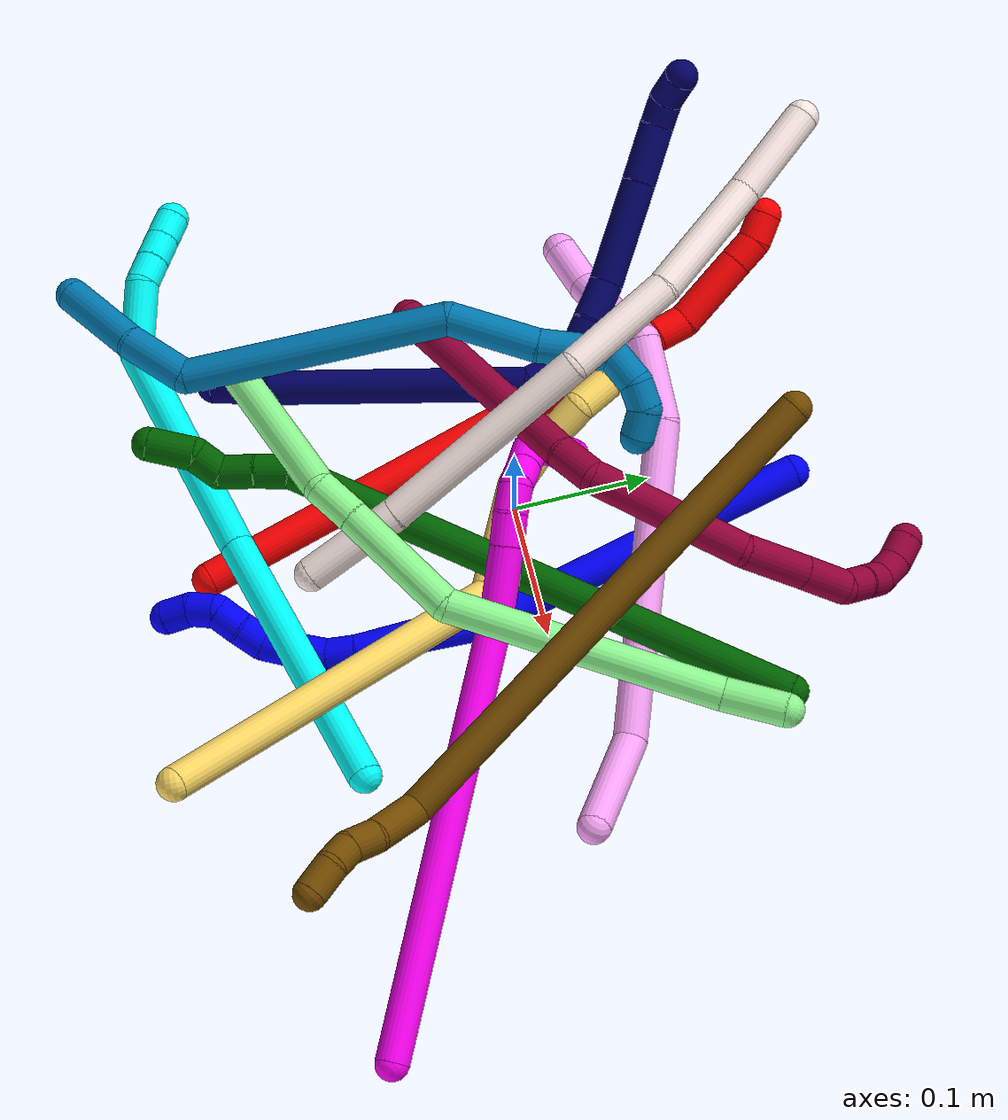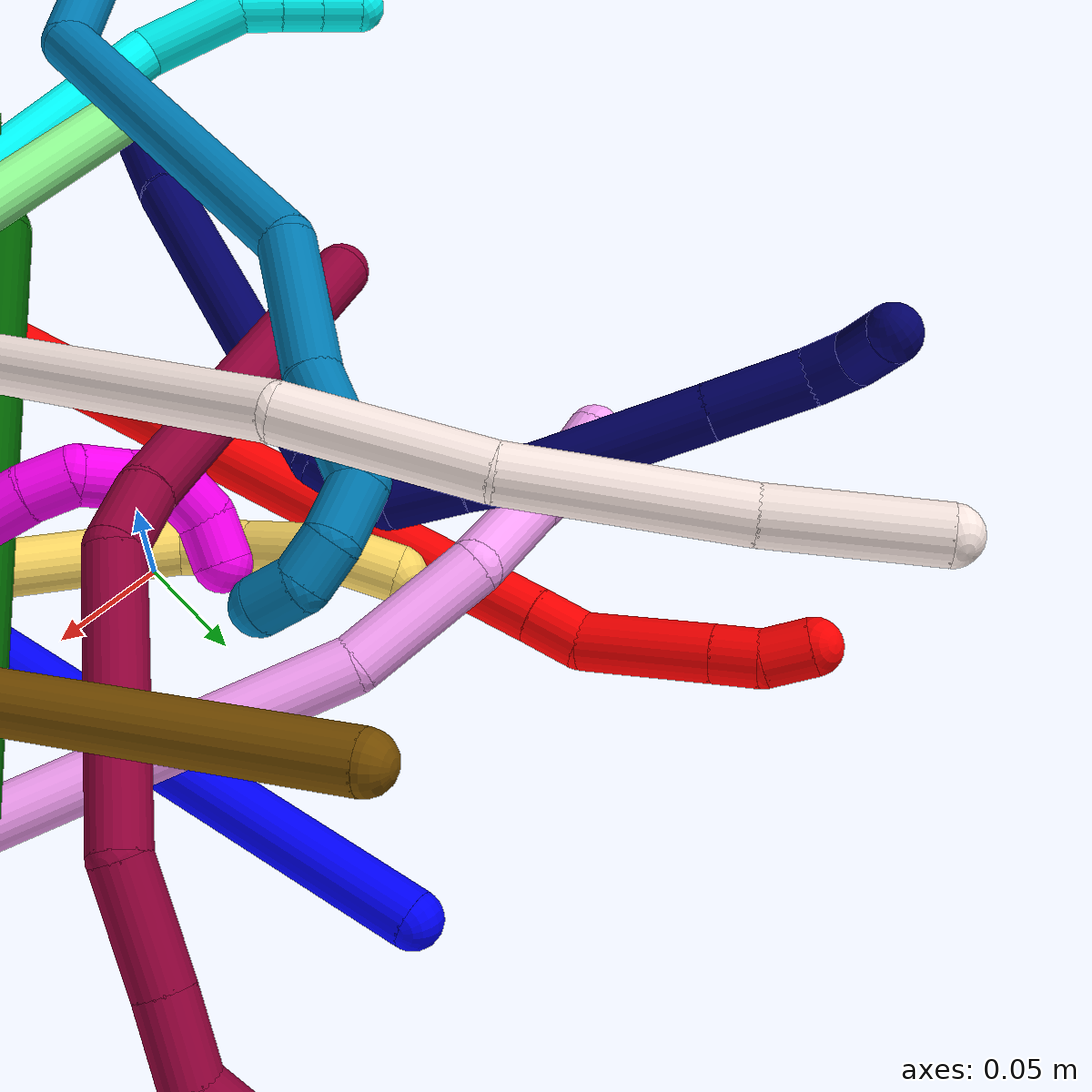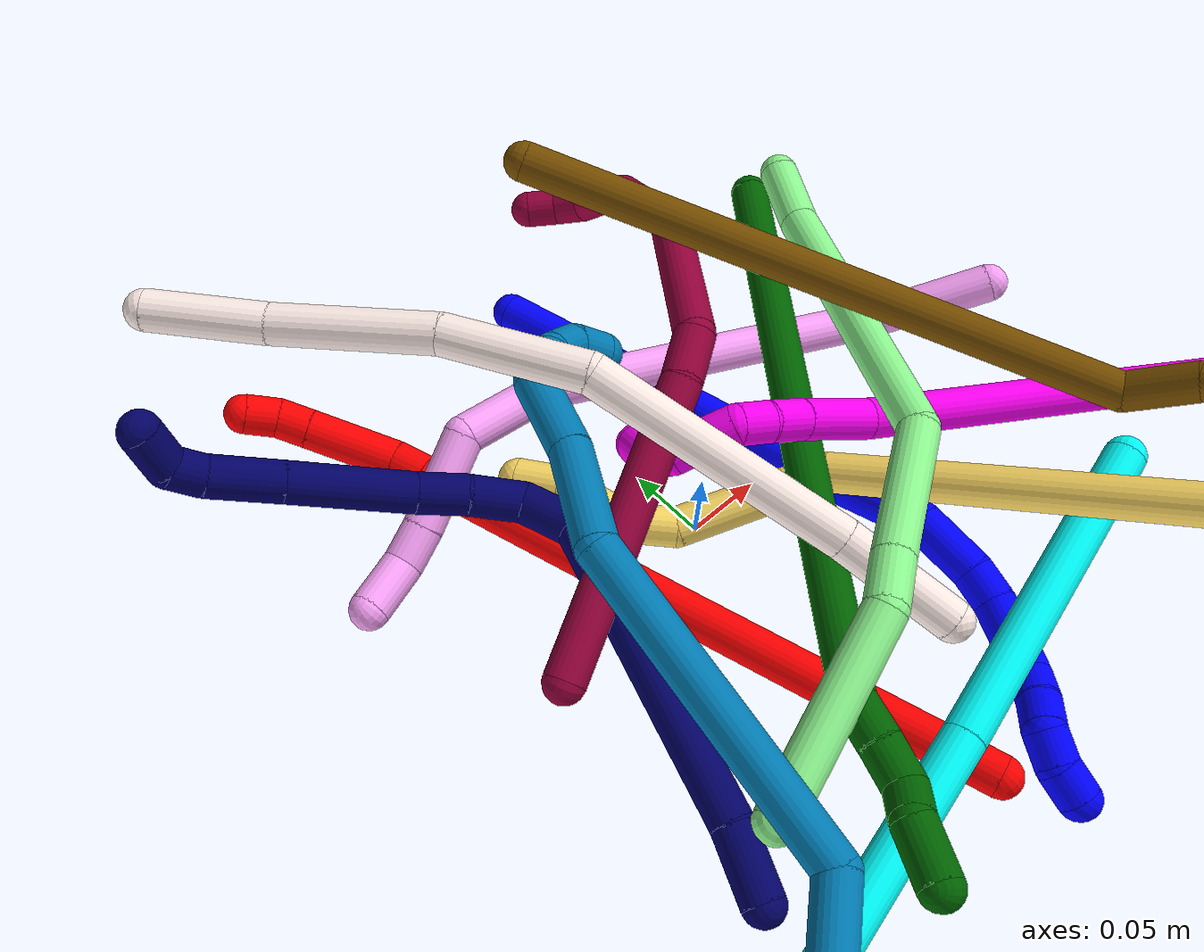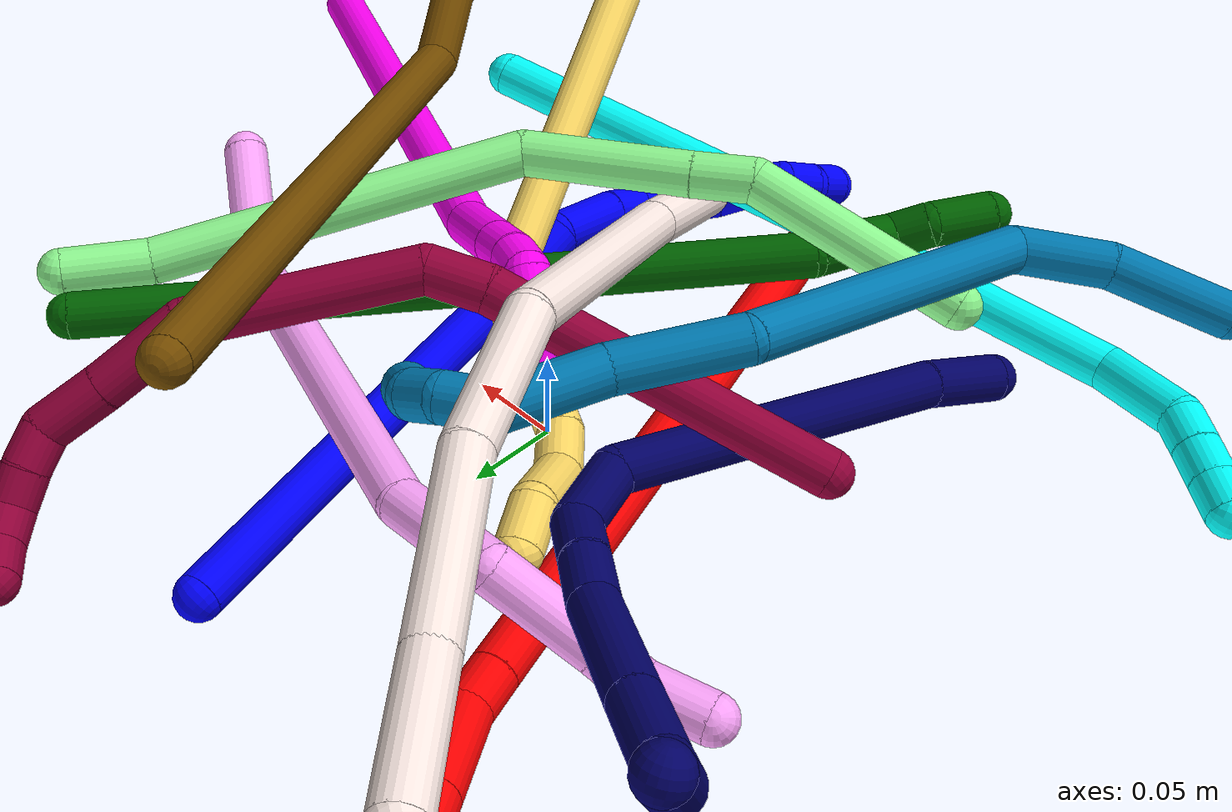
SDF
<sdf version="1.7">
 <world name="default">
  <plugin name="TubeGeneratorPlugin" filename="libtube_generator_plugin.so"/>
  <model name="photoneo_s_sensor">
   <static>1</static>
   <pose>0 0 2 1.57079 1.57079 3.14159</pose>
   <link name="link">
    <inertial><mass>0.1</mass></inertial>
    <sensor name="sensor" type="depth">
     <update_rate>30</update_rate>
     <camera>
      <horizontal_fov>1.22</horizontal_fov>
      <image><width>1920</width><height>1200</height><format>B8G8R8</format></image>
      <clip><near>0.1</near><far>4</far></clip>
      <depth_camera><output>points</output></depth_camera>
     </camera>
     <plugin name="camera_plugin" filename="libgazebo_ros_depth_camera.so">
      <baseline>0.2</baseline>
      <alwaysOn>1</alwaysOn>
      <updateRate>0.0</updateRate>
      <cameraName>camera_ir</cameraName>
      <imageTopicName>/camera/color/image_raw</imageTopicName>
      <cameraInfoTopicName>/camera/color/camera_info</cameraInfoTopicName>
      <depthImageTopicName>/camera/depth/image_raw</depthImageTopicName>
      <depthImageCameraInfoTopicName>/camera/depth/camera_info</depthImageCameraInfoTopicName>
      <pointCloudTopicName>/camera/depth/points</pointCloudTopicName>
      <frameName>fr_optical</frameName>
      <pointCloudCutoff>0.1</pointCloudCutoff>
      <pointCloudCutoffMax>2.0</pointCloudCutoffMax>
      <distortionK1>0</distortionK1>
      <distortionK2>0</distortionK2>
      <distortionK3>0</distortionK3>
      <distortionT1>0</distortionT1>
      <distortionT2>0</distortionT2>
      <CxPrime>0</CxPrime>
      <Cx>0</Cx>
      <Cy>0</Cy>
      <focalLength>0</focalLength>
      <hackBaseline>0</hackBaseline>
     </plugin>
    </sensor>
   </link>
  </model>
  <gravity>0 0 -9.8</gravity>
  <magnetic_field>6e-06 2.3e-05 -4.2e-05</magnetic_field>
  <atmosphere type="adiabatic"/>
  <physics name="default_physics" default="0" type="ode">
   <max_step_size>0.003</max_step_size>
   <real_time_factor>1</real_time_factor>
   <real_time_update_rate>1000</real_time_update_rate>
   <max_contacts>10000</max_contacts>
   <ode>
    <solver>
     <type>quick</type>
     <iters>100</iters>
     <sor>1.3</sor>
     <use_dynamic_moi_rescaling>0</use_dynamic_moi_rescaling>
    </solver>
    <constraints>
     <contact_max_correcting_vel>0</contact_max_correcting_vel>
     <contact_surface_layer>0.001</contact_surface_layer>
     <cfm>0</cfm>
     <erp>0.2</erp>
    </constraints>
   </ode>
  </physics>
  <scene><ambient>0.4 0.4 0.4 1</ambient><background>0.7 0.7 0.7 1</background><shadows>0</shadows></scene>
  <audio><device>default</device></audio>
  <spherical_coordinates>
   <surface_model>EARTH_WGS84</surface_model>
   <latitude_deg>0</latitude_deg>
   <longitude_deg>0</longitude_deg>
   <elevation>0</elevation>
   <heading_deg>0</heading_deg>
  </spherical_coordinates>
  <model name="bin">
   <static>1</static>
   <link name="bottom">
    <collision name="collision-bottom">
     <pose>0 0 -0.01 0 -0 0</pose>
     <geometry><box><size>0.8 0.6 0.02</size></box></geometry>
     <surface>
      <friction><ode><mu>100</mu><mu2>100</mu2></ode></friction>
      <contact><collide_bitmask>65535</collide_bitmask></contact>
     </surface>
    </collision>
   </link>
   <link name="west_wall">
    <collision name="collision-west_wall">
     <pose>-0.41 0 0.1 0 -0 0</pose>
     <geometry><box><size>0.02 0.6 0.2</size></box></geometry>
     <surface>
      <friction><ode><mu>100</mu><mu2>100</mu2></ode></friction>
      <contact><collide_bitmask>65535</collide_bitmask></contact>
     </surface>
    </collision>
   </link>
   <link name="east_wall">
    <collision name="collision-east_wall">
     <pose>0.41 0 0.1 0 -0 0</pose>
     <geometry><box><size>0.02 0.6 0.2</size></box></geometry>
     <surface>
      <friction><ode><mu>100</mu><mu2>100</mu2></ode></friction>
      <contact><collide_bitmask>65535</collide_bitmask></contact>
     </surface>
    </collision>
   </link>
   <link name="south_wall">
    <collision name="collision-south_wall">
     <pose>0 -0.31 0.1 0 -0 0</pose>
     <geometry><box><size>0.8 0.02 0.2</size></box></geometry>
     <surface>
      <friction><ode><mu>100</mu><mu2>100</mu2></ode></friction>
      <contact><collide_bitmask>65535</collide_bitmask></contact>
     </surface>
    </collision>
   </link>
   <link name="north_wall">
    <collision name="collision-north_wall">
     <pose>0 0.31 0.1 0 -0 0</pose>
     <geometry><box><size>0.8 0.02 0.2</size></box></geometry>
     <surface>
      <friction><ode><mu>100</mu><mu2>100</mu2></ode></friction>
      <contact><collide_bitmask>65535</collide_bitmask></contact>
     </surface>
    </collision>
   </link>
  </model>
  <model name="1">
   <static>0</static>
   <link name="1">
    <collision name="collision-cylinder-e_1_1_4">
     <pose>0.014286 -0.124227 0.009486 1.49459 0.114163 0.105794</pose>
     <geometry><cylinder><radius>0.0125</radius><length>0.25081</length></cylinder></geometry>
     <surface>
      <friction><ode><mu>1.16</mu><mu2>1.16</mu2><slip1>0</slip1><slip2>0</slip2></ode></friction>
      <contact><ode><kp>1e+06</kp><kd>1</kd><max_vel>0</max_vel><min_depth>0.001</min_depth></ode></contact>
     </surface>
    </collision>
    <visual name="visual-cylinder-e_1_1_4">
     <pose>0.014286 -0.124227 0.009486 1.49459 0.114163 0.105794</pose>
     <geometry><cylinder><radius>0.0125</radius><length>0.25081</length></cylinder></geometry>
     <material><ambient>0 0 1 1</ambient></material>
    </visual>
    <collision name="collision-cylinder-e_2_4_5">
     <pose>0.022051 -0.276736 0.021442 1.48367 -0.225746 -0.207028</pose>
     <geometry><cylinder><radius>0.0125</radius><length>0.058258</length></cylinder></geometry>
     <surface>
      <friction><ode><mu>1.16</mu><mu2>1.16</mu2><slip1>0</slip1><slip2>0</slip2></ode></friction>
      <contact><ode><kp>1e+06</kp><kd>1</kd><max_vel>0</max_vel><min_depth>0.001</min_depth></ode></contact>
     </surface>
    </collision>
    <visual name="visual-cylinder-e_2_4_5">
     <pose>0.022051 -0.276736 0.021442 1.48367 -0.225746 -0.207028</pose>
     <geometry><cylinder><radius>0.0125</radius><length>0.058258</length></cylinder></geometry>
     <material><ambient>0 0 1 1</ambient></material>
    </visual>
    <collision name="collision-cylinder-e_3_5_6">
     <pose>0.017915 -0.324898 0.019459 1.79115 0.116489 0.145377</pose>
     <geometry><cylinder><radius>0.0125</radius><length>0.041024</length></cylinder></geometry>
     <surface>
      <friction><ode><mu>1.16</mu><mu2>1.16</mu2><slip1>0</slip1><slip2>0</slip2></ode></friction>
      <contact><ode><kp>1e+06</kp><kd>1</kd><max_vel>0</max_vel><min_depth>0.001</min_depth></ode></contact>
     </surface>
    </collision>
    <visual name="visual-cylinder-e_3_5_6">
     <pose>0.017915 -0.324898 0.019459 1.79115 0.116489 0.145377</pose>
     <geometry><cylinder><radius>0.0125</radius><length>0.041024</length></cylinder></geometry>
     <material><ambient>0 0 1 1</ambient></material>
    </visual>
    <collision name="collision-cylinder-e_4_6_7">
     <pose>0.021464 -0.354697 0.010706 1.97986 0.107372 0.163369</pose>
     <geometry><cylinder><radius>0.0125</radius><length>0.021746</length></cylinder></geometry>
     <surface>
      <friction><ode><mu>1.16</mu><mu2>1.16</mu2><slip1>0</slip1><slip2>0</slip2></ode></friction>
      <contact><ode><kp>1e+06</kp><kd>1</kd><max_vel>0</max_vel><min_depth>0.001</min_depth></ode></contact>
     </surface>
    </collision>
    <visual name="visual-cylinder-e_4_6_7">
     <pose>0.021464 -0.354697 0.010706 1.97986 0.107372 0.163369</pose>
     <geometry><cylinder><radius>0.0125</radius><length>0.021746</length></cylinder></geometry>
     <material><ambient>0 0 1 1</ambient></material>
    </visual>
    <collision name="collision-cylinder-e_5_7_8">
     <pose>0.02051 -0.376256 -0.001041 2.13992 -0.152204 -0.276813</pose>
     <geometry><cylinder><radius>0.0125</radius><length>0.027961</length></cylinder></geometry>
     <surface>
      <friction><ode><mu>1.16</mu><mu2>1.16</mu2><slip1>0</slip1><slip2>0</slip2></ode></friction>
      <contact><ode><kp>1e+06</kp><kd>1</kd><max_vel>0</max_vel><min_depth>0.001</min_depth></ode></contact>
     </surface>
    </collision>
    <visual name="visual-cylinder-e_5_7_8">
     <pose>0.02051 -0.376256 -0.001041 2.13992 -0.152204 -0.276813</pose>
     <geometry><cylinder><radius>0.0125</radius><length>0.027961</length></cylinder></geometry>
     <material><ambient>0 0 1 1</ambient></material>
    </visual>
    <collision name="collision-cylinder-e_6_8_9">
     <pose>0.016345 -0.396123 -0.013864 2.14971 -0.205152 -0.37602</pose>
     <geometry><cylinder><radius>0.0125</radius><length>0.020076</length></cylinder></geometry>
     <surface>
      <friction><ode><mu>1.16</mu><mu2>1.16</mu2><slip1>0</slip1><slip2>0</slip2></ode></friction>
      <contact><ode><kp>1e+06</kp><kd>1</kd><max_vel>0</max_vel><min_depth>0.001</min_depth></ode></contact>
     </surface>
    </collision>
    <visual name="visual-cylinder-e_6_8_9">
     <pose>0.016345 -0.396123 -0.013864 2.14971 -0.205152 -0.37602</pose>
     <geometry><cylinder><radius>0.0125</radius><length>0.020076</length></cylinder></geometry>
     <material><ambient>0 0 1 1</ambient></material>
    </visual>
    <collision name="collision-cylinder-e_7_9_10">
     <pose>0.008152 -0.410579 -0.024082 2.23134 -0.661951 -1.2243</pose>
     <geometry><cylinder><radius>0.0125</radius><length>0.020006</length></cylinder></geometry>
     <surface>
      <friction><ode><mu>1.16</mu><mu2>1.16</mu2><slip1>0</slip1><slip2>0</slip2></ode></friction>
      <contact><ode><kp>1e+06</kp><kd>1</kd><max_vel>0</max_vel><min_depth>0.001</min_depth></ode></contact>
     </surface>
    </collision>
    <visual name="visual-cylinder-e_7_9_10">
     <pose>0.008152 -0.410579 -0.024082 2.23134 -0.661951 -1.2243</pose>
     <geometry><cylinder><radius>0.0125</radius><length>0.020006</length></cylinder></geometry>
     <material><ambient>0 0 1 1</ambient></material>
    </visual>
    <collision name="collision-cylinder-e_8_10_11">
     <pose>-0.003493 -0.422564 -0.035025 2.38549 -0.58013 -1.28899</pose>
     <geometry><cylinder><radius>0.0125</radius><length>0.020056</length></cylinder></geometry>
     <surface>
      <friction><ode><mu>1.16</mu><mu2>1.16</mu2><slip1>0</slip1><slip2>0</slip2></ode></friction>
      <contact><ode><kp>1e+06</kp><kd>1</kd><max_vel>0</max_vel><min_depth>0.001</min_depth></ode></contact>
     </surface>
    </collision>
    <visual name="visual-cylinder-e_8_10_11">
     <pose>-0.003493 -0.422564 -0.035025 2.38549 -0.58013 -1.28899</pose>
     <geometry><cylinder><radius>0.0125</radius><length>0.020056</length></cylinder></geometry>
     <material><ambient>0 0 1 1</ambient></material>
    </visual>
    <collision name="collision-cylinder-e_9_11_12">
     <pose>-0.008362 -0.436161 -0.047344 2.24113 0.062663 0.129507</pose>
     <geometry><cylinder><radius>0.0125</radius><length>0.020054</length></cylinder></geometry>
     <surface>
      <friction><ode><mu>1.16</mu><mu2>1.16</mu2><slip1>0</slip1><slip2>0</slip2></ode></friction>
      <contact><ode><kp>1e+06</kp><kd>1</kd><max_vel>0</max_vel><min_depth>0.001</min_depth></ode></contact>
     </surface>
    </collision>
    <visual name="visual-cylinder-e_9_11_12">
     <pose>-0.008362 -0.436161 -0.047344 2.24113 0.062663 0.129507</pose>
     <geometry><cylinder><radius>0.0125</radius><length>0.020054</length></cylinder></geometry>
     <material><ambient>0 0 1 1</ambient></material>
    </visual>
    <collision name="collision-cylinder-e_10_12_2">
     <pose>-0.004368 -0.452542 -0.057544 2.00719 0.343042 0.531009</pose>
     <geometry><cylinder><radius>0.0125</radius><length>0.02001</length></cylinder></geometry>
     <surface>
      <friction><ode><mu>1.16</mu><mu2>1.16</mu2><slip1>0</slip1><slip2>0</slip2></ode></friction>
      <contact><ode><kp>1e+06</kp><kd>1</kd><max_vel>0</max_vel><min_depth>0.001</min_depth></ode></contact>
     </surface>
    </collision>
    <visual name="visual-cylinder-e_10_12_2">
     <pose>-0.004368 -0.452542 -0.057544 2.00719 0.343042 0.531009</pose>
     <geometry><cylinder><radius>0.0125</radius><length>0.02001</length></cylinder></geometry>
     <material><ambient>0 0 1 1</ambient></material>
    </visual>
    <collision name="collision-sphere-2">
     <pose>-0.001003 -0.461081 -0.061526 0 -0 0</pose>
     <geometry><sphere><radius>0.0125</radius></sphere></geometry>
     <surface>
      <friction><ode><mu>1.16</mu><mu2>1.16</mu2><slip1>0</slip1><slip2>0</slip2></ode></friction>
      <contact><ode><kp>1e+06</kp><kd>1</kd><max_vel>0</max_vel><min_depth>0.001</min_depth></ode></contact>
     </surface>
    </collision>
    <visual name="visual-sphere-2">
     <pose>-0.001003 -0.461081 -0.061526 0 -0 0</pose>
     <geometry><sphere><radius>0.0125</radius></sphere></geometry>
     <material><ambient>0 0 1 1</ambient></material>
    </visual>
    <collision name="collision-sphere-12">
     <pose>-0.007734 -0.444003 -0.053561 0 -0 0</pose>
     <geometry><sphere><radius>0.0125</radius></sphere></geometry>
     <surface>
      <friction><ode><mu>1.16</mu><mu2>1.16</mu2><slip1>0</slip1><slip2>0</slip2></ode></friction>
      <contact><ode><kp>1e+06</kp><kd>1</kd><max_vel>0</max_vel><min_depth>0.001</min_depth></ode></contact>
     </surface>
    </collision>
    <visual name="visual-sphere-12">
     <pose>-0.007734 -0.444003 -0.053561 0 -0 0</pose>
     <geometry><sphere><radius>0.0125</radius></sphere></geometry>
     <material><ambient>0 0 1 1</ambient></material>
    </visual>
    <collision name="collision-sphere-11">
     <pose>-0.00899 -0.428319 -0.041127 0 -0 0</pose>
     <geometry><sphere><radius>0.0125</radius></sphere></geometry>
     <surface>
      <friction><ode><mu>1.16</mu><mu2>1.16</mu2><slip1>0</slip1><slip2>0</slip2></ode></friction>
      <contact><ode><kp>1e+06</kp><kd>1</kd><max_vel>0</max_vel><min_depth>0.001</min_depth></ode></contact>
     </surface>
    </collision>
    <visual name="visual-sphere-11">
     <pose>-0.00899 -0.428319 -0.041127 0 -0 0</pose>
     <geometry><sphere><radius>0.0125</radius></sphere></geometry>
     <material><ambient>0 0 1 1</ambient></material>
    </visual>
    <collision name="collision-sphere-10">
     <pose>0.002004 -0.41681 -0.028923 0 -0 0</pose>
     <geometry><sphere><radius>0.0125</radius></sphere></geometry>
     <surface>
      <friction><ode><mu>1.16</mu><mu2>1.16</mu2><slip1>0</slip1><slip2>0</slip2></ode></friction>
      <contact><ode><kp>1e+06</kp><kd>1</kd><max_vel>0</max_vel><min_depth>0.001</min_depth></ode></contact>
     </surface>
    </collision>
    <visual name="visual-sphere-10">
     <pose>0.002004 -0.41681 -0.028923 0 -0 0</pose>
     <geometry><sphere><radius>0.0125</radius></sphere></geometry>
     <material><ambient>0 0 1 1</ambient></material>
    </visual>
    <collision name="collision-sphere-9">
     <pose>0.014301 -0.404349 -0.019241 0 -0 0</pose>
     <geometry><sphere><radius>0.0125</radius></sphere></geometry>
     <surface>
      <friction><ode><mu>1.16</mu><mu2>1.16</mu2><slip1>0</slip1><slip2>0</slip2></ode></friction>
      <contact><ode><kp>1e+06</kp><kd>1</kd><max_vel>0</max_vel><min_depth>0.001</min_depth></ode></contact>
     </surface>
    </collision>
    <visual name="visual-sphere-9">
     <pose>0.014301 -0.404349 -0.019241 0 -0 0</pose>
     <geometry><sphere><radius>0.0125</radius></sphere></geometry>
     <material><ambient>0 0 1 1</ambient></material>
    </visual>
    <collision name="collision-sphere-4">
     <pose>0.028571 -0.248454 0.018972 0 -0 0</pose>
     <geometry><sphere><radius>0.0125</radius></sphere></geometry>
     <surface>
      <friction><ode><mu>1.16</mu><mu2>1.16</mu2><slip1>0</slip1><slip2>0</slip2></ode></friction>
      <contact><ode><kp>1e+06</kp><kd>1</kd><max_vel>0</max_vel><min_depth>0.001</min_depth></ode></contact>
     </surface>
    </collision>
    <visual name="visual-sphere-4">
     <pose>0.028571 -0.248454 0.018972 0 -0 0</pose>
     <geometry><sphere><radius>0.0125</radius></sphere></geometry>
     <material><ambient>0 0 1 1</ambient></material>
    </visual>
    <collision name="collision-sphere-1">
     <geometry><sphere><radius>0.0125</radius></sphere></geometry>
     <surface>
      <friction><ode><mu>1.16</mu><mu2>1.16</mu2><slip1>0</slip1><slip2>0</slip2></ode></friction>
      <contact><ode><kp>1e+06</kp><kd>1</kd><max_vel>0</max_vel><min_depth>0.001</min_depth></ode></contact>
     </surface>
    </collision>
    <visual name="visual-sphere-1">
     <geometry><sphere><radius>0.0125</radius></sphere></geometry>
     <material><ambient>0 0 1 1</ambient></material>
    </visual>
    <collision name="collision-sphere-8">
     <pose>0.01839 -0.387897 -0.008488 0 -0 0</pose>
     <geometry><sphere><radius>0.0125</radius></sphere></geometry>
     <surface>
      <friction><ode><mu>1.16</mu><mu2>1.16</mu2><slip1>0</slip1><slip2>0</slip2></ode></friction>
      <contact><ode><kp>1e+06</kp><kd>1</kd><max_vel>0</max_vel><min_depth>0.001</min_depth></ode></contact>
     </surface>
    </collision>
    <visual name="visual-sphere-8">
     <pose>0.01839 -0.387897 -0.008488 0 -0 0</pose>
     <geometry><sphere><radius>0.0125</radius></sphere></geometry>
     <material><ambient>0 0 1 1</ambient></material>
    </visual>
    <collision name="collision-sphere-5">
     <pose>0.015531 -0.305018 0.023912 0 -0 0</pose>
     <geometry><sphere><radius>0.0125</radius></sphere></geometry>
     <surface>
      <friction><ode><mu>1.16</mu><mu2>1.16</mu2><slip1>0</slip1><slip2>0</slip2></ode></friction>
      <contact><ode><kp>1e+06</kp><kd>1</kd><max_vel>0</max_vel><min_depth>0.001</min_depth></ode></contact>
     </surface>
    </collision>
    <visual name="visual-sphere-5">
     <pose>0.015531 -0.305018 0.023912 0 -0 0</pose>
     <geometry><sphere><radius>0.0125</radius></sphere></geometry>
     <material><ambient>0 0 1 1</ambient></material>
    </visual>
    <collision name="collision-sphere-6">
     <pose>0.020299 -0.344779 0.015006 0 -0 0</pose>
     <geometry><sphere><radius>0.0125</radius></sphere></geometry>
     <surface>
      <friction><ode><mu>1.16</mu><mu2>1.16</mu2><slip1>0</slip1><slip2>0</slip2></ode></friction>
      <contact><ode><kp>1e+06</kp><kd>1</kd><max_vel>0</max_vel><min_depth>0.001</min_depth></ode></contact>
     </surface>
    </collision>
    <visual name="visual-sphere-6">
     <pose>0.020299 -0.344779 0.015006 0 -0 0</pose>
     <geometry><sphere><radius>0.0125</radius></sphere></geometry>
     <material><ambient>0 0 1 1</ambient></material>
    </visual>
    <collision name="collision-sphere-7">
     <pose>0.02263 -0.364616 0.006406 0 -0 0</pose>
     <geometry><sphere><radius>0.0125</radius></sphere></geometry>
     <surface>
      <friction><ode><mu>1.16</mu><mu2>1.16</mu2><slip1>0</slip1><slip2>0</slip2></ode></friction>
      <contact><ode><kp>1e+06</kp><kd>1</kd><max_vel>0</max_vel><min_depth>0.001</min_depth></ode></contact>
     </surface>
    </collision>
    <visual name="visual-sphere-7">
     <pose>0.02263 -0.364616 0.006406 0 -0 0</pose>
     <geometry><sphere><radius>0.0125</radius></sphere></geometry>
     <material><ambient>0 0 1 1</ambient></material>
    </visual>
    <inertial>
     <pose>0.013618 -0.24257 0.002134 0 -0 0</pose>
     <mass>0.5</mass>
     <inertia>
      <ixx>0.001477</ixx>
      <ixy>0</ixy>
      <ixz>0</ixz>
      <iyy>0.000212</iyy>
      <iyz>0</iyz>
      <izz>0.001196</izz>
     </inertia>
    </inertial>
   </link>
   <pose>0.024946 0.202003 0.011492 -0.12886 1.05824 0.006364</pose>
  </model>
  <model name="2">
   <static>0</static>
   <link name="2">
    <collision name="collision-cylinder-e_1_1_4">
     <pose>-0.039215 0.130053 0.130662 -0.783063 -0.209591 0.086792</pose>
     <geometry><cylinder><radius>0.0125</radius><length>0.376956</length></cylinder></geometry>
     <surface>
      <friction><ode><mu>1.16</mu><mu2>1.16</mu2><slip1>0</slip1><slip2>0</slip2></ode></friction>
      <contact><ode><kp>1e+06</kp><kd>1</kd><max_vel>0</max_vel><min_depth>0.001</min_depth></ode></contact>
     </surface>
    </collision>
    <visual name="visual-cylinder-e_1_1_4">
     <pose>-0.039215 0.130053 0.130662 -0.783063 -0.209591 0.086792</pose>
     <geometry><cylinder><radius>0.0125</radius><length>0.376956</length></cylinder></geometry>
     <material><ambient>1 0 0 1</ambient></material>
    </visual>
    <collision name="collision-cylinder-e_2_4_5">
     <pose>-0.080954 0.26849 0.269183 -0.817673 -0.216257 0.093991</pose>
     <geometry><cylinder><radius>0.0125</radius><length>0.023531</length></cylinder></geometry>
     <surface>
      <friction><ode><mu>1.16</mu><mu2>1.16</mu2><slip1>0</slip1><slip2>0</slip2></ode></friction>
      <contact><ode><kp>1e+06</kp><kd>1</kd><max_vel>0</max_vel><min_depth>0.001</min_depth></ode></contact>
     </surface>
    </collision>
    <visual name="visual-cylinder-e_2_4_5">
     <pose>-0.080954 0.26849 0.269183 -0.817673 -0.216257 0.093991</pose>
     <geometry><cylinder><radius>0.0125</radius><length>0.023531</length></cylinder></geometry>
     <material><ambient>1 0 0 1</ambient></material>
    </visual>
    <collision name="collision-cylinder-e_3_5_6">
     <pose>-0.094917 0.28834 0.300797 -0.44973 -0.409168 0.094847</pose>
     <geometry><cylinder><radius>0.0125</radius><length>0.057502</length></cylinder></geometry>
     <surface>
      <friction><ode><mu>1.16</mu><mu2>1.16</mu2><slip1>0</slip1><slip2>0</slip2></ode></friction>
      <contact><ode><kp>1e+06</kp><kd>1</kd><max_vel>0</max_vel><min_depth>0.001</min_depth></ode></contact>
     </surface>
    </collision>
    <visual name="visual-cylinder-e_3_5_6">
     <pose>-0.094917 0.28834 0.300797 -0.44973 -0.409168 0.094847</pose>
     <geometry><cylinder><radius>0.0125</radius><length>0.057502</length></cylinder></geometry>
     <material><ambient>1 0 0 1</ambient></material>
    </visual>
    <collision name="collision-cylinder-e_4_6_7">
     <pose>-0.11047 0.304019 0.333016 -0.461683 -0.410441 0.097766</pose>
     <geometry><cylinder><radius>0.0125</radius><length>0.020621</length></cylinder></geometry>
     <surface>
      <friction><ode><mu>1.16</mu><mu2>1.16</mu2><slip1>0</slip1><slip2>0</slip2></ode></friction>
      <contact><ode><kp>1e+06</kp><kd>1</kd><max_vel>0</max_vel><min_depth>0.001</min_depth></ode></contact>
     </surface>
    </collision>
    <visual name="visual-cylinder-e_4_6_7">
     <pose>-0.11047 0.304019 0.333016 -0.461683 -0.410441 0.097766</pose>
     <geometry><cylinder><radius>0.0125</radius><length>0.020621</length></cylinder></geometry>
     <material><ambient>1 0 0 1</ambient></material>
    </visual>
    <collision name="collision-cylinder-e_5_7_2">
     <pose>-0.121205 0.309784 0.349734 -0.186126 -0.667612 0.06471</pose>
     <geometry><cylinder><radius>0.0125</radius><length>0.021389</length></cylinder></geometry>
     <surface>
      <friction><ode><mu>1.16</mu><mu2>1.16</mu2><slip1>0</slip1><slip2>0</slip2></ode></friction>
      <contact><ode><kp>1e+06</kp><kd>1</kd><max_vel>0</max_vel><min_depth>0.001</min_depth></ode></contact>
     </surface>
    </collision>
    <visual name="visual-cylinder-e_5_7_2">
     <pose>-0.121205 0.309784 0.349734 -0.186126 -0.667612 0.06471</pose>
     <geometry><cylinder><radius>0.0125</radius><length>0.021389</length></cylinder></geometry>
     <material><ambient>1 0 0 1</ambient></material>
    </visual>
    <collision name="collision-sphere-2">
     <pose>-0.127826 0.311338 0.357987 0 -0 0</pose>
     <geometry><sphere><radius>0.0125</radius></sphere></geometry>
     <surface>
      <friction><ode><mu>1.16</mu><mu2>1.16</mu2><slip1>0</slip1><slip2>0</slip2></ode></friction>
      <contact><ode><kp>1e+06</kp><kd>1</kd><max_vel>0</max_vel><min_depth>0.001</min_depth></ode></contact>
     </surface>
    </collision>
    <visual name="visual-sphere-2">
     <pose>-0.127826 0.311338 0.357987 0 -0 0</pose>
     <geometry><sphere><radius>0.0125</radius></sphere></geometry>
     <material><ambient>1 0 0 1</ambient></material>
    </visual>
    <collision name="collision-sphere-7">
     <pose>-0.114584 0.30823 0.34148 0 -0 0</pose>
     <geometry><sphere><radius>0.0125</radius></sphere></geometry>
     <surface>
      <friction><ode><mu>1.16</mu><mu2>1.16</mu2><slip1>0</slip1><slip2>0</slip2></ode></friction>
      <contact><ode><kp>1e+06</kp><kd>1</kd><max_vel>0</max_vel><min_depth>0.001</min_depth></ode></contact>
     </surface>
    </collision>
    <visual name="visual-sphere-7">
     <pose>-0.114584 0.30823 0.34148 0 -0 0</pose>
     <geometry><sphere><radius>0.0125</radius></sphere></geometry>
     <material><ambient>1 0 0 1</ambient></material>
    </visual>
    <collision name="collision-sphere-6">
     <pose>-0.106356 0.299807 0.324552 0 -0 0</pose>
     <geometry><sphere><radius>0.0125</radius></sphere></geometry>
     <surface>
      <friction><ode><mu>1.16</mu><mu2>1.16</mu2><slip1>0</slip1><slip2>0</slip2></ode></friction>
      <contact><ode><kp>1e+06</kp><kd>1</kd><max_vel>0</max_vel><min_depth>0.001</min_depth></ode></contact>
     </surface>
    </collision>
    <visual name="visual-sphere-6">
     <pose>-0.106356 0.299807 0.324552 0 -0 0</pose>
     <geometry><sphere><radius>0.0125</radius></sphere></geometry>
     <material><ambient>1 0 0 1</ambient></material>
    </visual>
    <collision name="collision-sphere-5">
     <pose>-0.083479 0.276873 0.277042 0 -0 0</pose>
     <geometry><sphere><radius>0.0125</radius></sphere></geometry>
     <surface>
      <friction><ode><mu>1.16</mu><mu2>1.16</mu2><slip1>0</slip1><slip2>0</slip2></ode></friction>
      <contact><ode><kp>1e+06</kp><kd>1</kd><max_vel>0</max_vel><min_depth>0.001</min_depth></ode></contact>
     </surface>
    </collision>
    <visual name="visual-sphere-5">
     <pose>-0.083479 0.276873 0.277042 0 -0 0</pose>
     <geometry><sphere><radius>0.0125</radius></sphere></geometry>
     <material><ambient>1 0 0 1</ambient></material>
    </visual>
    <collision name="collision-sphere-1">
     <geometry><sphere><radius>0.0125</radius></sphere></geometry>
     <surface>
      <friction><ode><mu>1.16</mu><mu2>1.16</mu2><slip1>0</slip1><slip2>0</slip2></ode></friction>
      <contact><ode><kp>1e+06</kp><kd>1</kd><max_vel>0</max_vel><min_depth>0.001</min_depth></ode></contact>
     </surface>
    </collision>
    <visual name="visual-sphere-1">
     <geometry><sphere><radius>0.0125</radius></sphere></geometry>
     <material><ambient>1 0 0 1</ambient></material>
    </visual>
    <collision name="collision-sphere-4">
     <pose>-0.078429 0.260106 0.261323 0 -0 0</pose>
     <geometry><sphere><radius>0.0125</radius></sphere></geometry>
     <surface>
      <friction><ode><mu>1.16</mu><mu2>1.16</mu2><slip1>0</slip1><slip2>0</slip2></ode></friction>
      <contact><ode><kp>1e+06</kp><kd>1</kd><max_vel>0</max_vel><min_depth>0.001</min_depth></ode></contact>
     </surface>
    </collision>
    <visual name="visual-sphere-4">
     <pose>-0.078429 0.260106 0.261323 0 -0 0</pose>
     <geometry><sphere><radius>0.0125</radius></sphere></geometry>
     <material><ambient>1 0 0 1</ambient></material>
    </visual>
    <inertial>
     <pose>-0.054031 0.169635 0.174464 0 -0 0</pose>
     <mass>0.5</mass>
     <inertia>
      <ixx>0.004757</ixx>
      <ixy>0</ixy>
      <ixz>0</ixz>
      <iyy>0.003646</iyy>
      <iyz>0</iyz>
      <izz>-0.002131</izz>
     </inertia>
    </inertial>
   </link>
   <pose>0.004732 -0.227502 0.011497 -0.728358 -0.262708 0.072572</pose>
  </model>
  <model name="3">
   <static>0</static>
   <link name="3">
    <collision name="collision-cylinder-e_1_1_4">
     <pose>-0.011237 -0.01058 0.101671 0.103687 -0.109486 -0.005687</pose>
     <geometry><cylinder><radius>0.0125</radius><length>0.205671</length></cylinder></geometry>
     <surface>
      <friction><ode><mu>1.16</mu><mu2>1.16</mu2><slip1>0</slip1><slip2>0</slip2></ode></friction>
      <contact><ode><kp>1e+06</kp><kd>1</kd><max_vel>0</max_vel><min_depth>0.001</min_depth></ode></contact>
     </surface>
    </collision>
    <visual name="visual-cylinder-e_1_1_4">
     <pose>-0.011237 -0.01058 0.101671 0.103687 -0.109486 -0.005687</pose>
     <geometry><cylinder><radius>0.0125</radius><length>0.205671</length></cylinder></geometry>
     <material><ambient>0.003922 1 0.996078 1</ambient></material>
    </visual>
    <collision name="collision-cylinder-e_2_4_5">
     <pose>-0.03199 -0.03312 0.292135 0.13389 -0.105821 -0.007101</pose>
     <geometry><cylinder><radius>0.0125</radius><length>0.1802</length></cylinder></geometry>
     <surface>
      <friction><ode><mu>1.16</mu><mu2>1.16</mu2><slip1>0</slip1><slip2>0</slip2></ode></friction>
      <contact><ode><kp>1e+06</kp><kd>1</kd><max_vel>0</max_vel><min_depth>0.001</min_depth></ode></contact>
     </surface>
    </collision>
    <visual name="visual-cylinder-e_2_4_5">
     <pose>-0.03199 -0.03312 0.292135 0.13389 -0.105821 -0.007101</pose>
     <geometry><cylinder><radius>0.0125</radius><length>0.1802</length></cylinder></geometry>
     <material><ambient>0.003922 1 0.996078 1</ambient></material>
    </visual>
    <collision name="collision-cylinder-e_3_5_6">
     <pose>-0.056341 -0.055739 0.400356 0.501825 -0.589955 -0.155444</pose>
     <geometry><cylinder><radius>0.0125</radius><length>0.053332</length></cylinder></geometry>
     <surface>
      <friction><ode><mu>1.16</mu><mu2>1.16</mu2><slip1>0</slip1><slip2>0</slip2></ode></friction>
      <contact><ode><kp>1e+06</kp><kd>1</kd><max_vel>0</max_vel><min_depth>0.001</min_depth></ode></contact>
     </surface>
    </collision>
    <visual name="visual-cylinder-e_3_5_6">
     <pose>-0.056341 -0.055739 0.400356 0.501825 -0.589955 -0.155444</pose>
     <geometry><cylinder><radius>0.0125</radius><length>0.053332</length></cylinder></geometry>
     <material><ambient>0.003922 1 0.996078 1</ambient></material>
    </visual>
    <collision name="collision-cylinder-e_4_6_7">
     <pose>-0.074827 -0.073808 0.425707 0.896368 -0.367305 -0.178147</pose>
     <geometry><cylinder><radius>0.0125</radius><length>0.020331</length></cylinder></geometry>
     <surface>
      <friction><ode><mu>1.16</mu><mu2>1.16</mu2><slip1>0</slip1><slip2>0</slip2></ode></friction>
      <contact><ode><kp>1e+06</kp><kd>1</kd><max_vel>0</max_vel><min_depth>0.001</min_depth></ode></contact>
     </surface>
    </collision>
    <visual name="visual-cylinder-e_4_6_7">
     <pose>-0.074827 -0.073808 0.425707 0.896368 -0.367305 -0.178147</pose>
     <geometry><cylinder><radius>0.0125</radius><length>0.020331</length></cylinder></geometry>
     <material><ambient>0.003922 1 0.996078 1</ambient></material>
    </visual>
    <collision name="collision-cylinder-e_5_7_8">
     <pose>-0.081858 -0.088764 0.437582 0.903092 -0.338258 -0.165248</pose>
     <geometry><cylinder><radius>0.0125</radius><length>0.020373</length></cylinder></geometry>
     <surface>
      <friction><ode><mu>1.16</mu><mu2>1.16</mu2><slip1>0</slip1><slip2>0</slip2></ode></friction>
      <contact><ode><kp>1e+06</kp><kd>1</kd><max_vel>0</max_vel><min_depth>0.001</min_depth></ode></contact>
     </surface>
    </collision>
    <visual name="visual-cylinder-e_5_7_8">
     <pose>-0.081858 -0.088764 0.437582 0.903092 -0.338258 -0.165248</pose>
     <geometry><cylinder><radius>0.0125</radius><length>0.020373</length></cylinder></geometry>
     <material><ambient>0.003922 1 0.996078 1</ambient></material>
    </visual>
    <collision name="collision-cylinder-e_6_8_2">
     <pose>-0.088617 -0.103747 0.449379 0.904483 -0.343023 -0.167906</pose>
     <geometry><cylinder><radius>0.0125</radius><length>0.020093</length></cylinder></geometry>
     <surface>
      <friction><ode><mu>1.16</mu><mu2>1.16</mu2><slip1>0</slip1><slip2>0</slip2></ode></friction>
      <contact><ode><kp>1e+06</kp><kd>1</kd><max_vel>0</max_vel><min_depth>0.001</min_depth></ode></contact>
     </surface>
    </collision>
    <visual name="visual-cylinder-e_6_8_2">
     <pose>-0.088617 -0.103747 0.449379 0.904483 -0.343023 -0.167906</pose>
     <geometry><cylinder><radius>0.0125</radius><length>0.020093</length></cylinder></geometry>
     <material><ambient>0.003922 1 0.996078 1</ambient></material>
    </visual>
    <collision name="collision-sphere-2">
     <pose>-0.091996 -0.111185 0.455227 0 -0 0</pose>
     <geometry><sphere><radius>0.0125</radius></sphere></geometry>
     <surface>
      <friction><ode><mu>1.16</mu><mu2>1.16</mu2><slip1>0</slip1><slip2>0</slip2></ode></friction>
      <contact><ode><kp>1e+06</kp><kd>1</kd><max_vel>0</max_vel><min_depth>0.001</min_depth></ode></contact>
     </surface>
    </collision>
    <visual name="visual-sphere-2">
     <pose>-0.091996 -0.111185 0.455227 0 -0 0</pose>
     <geometry><sphere><radius>0.0125</radius></sphere></geometry>
     <material><ambient>0.003922 1 0.996078 1</ambient></material>
    </visual>
    <collision name="collision-sphere-4">
     <pose>-0.022473 -0.02116 0.203341 0 -0 0</pose>
     <geometry><sphere><radius>0.0125</radius></sphere></geometry>
     <surface>
      <friction><ode><mu>1.16</mu><mu2>1.16</mu2><slip1>0</slip1><slip2>0</slip2></ode></friction>
      <contact><ode><kp>1e+06</kp><kd>1</kd><max_vel>0</max_vel><min_depth>0.001</min_depth></ode></contact>
     </surface>
    </collision>
    <visual name="visual-sphere-4">
     <pose>-0.022473 -0.02116 0.203341 0 -0 0</pose>
     <geometry><sphere><radius>0.0125</radius></sphere></geometry>
     <material><ambient>0.003922 1 0.996078 1</ambient></material>
    </visual>
    <collision name="collision-sphere-1">
     <geometry><sphere><radius>0.0125</radius></sphere></geometry>
     <surface>
      <friction><ode><mu>1.16</mu><mu2>1.16</mu2><slip1>0</slip1><slip2>0</slip2></ode></friction>
      <contact><ode><kp>1e+06</kp><kd>1</kd><max_vel>0</max_vel><min_depth>0.001</min_depth></ode></contact>
     </surface>
    </collision>
    <visual name="visual-sphere-1">
     <geometry><sphere><radius>0.0125</radius></sphere></geometry>
     <material><ambient>0.003922 1 0.996078 1</ambient></material>
    </visual>
    <collision name="collision-sphere-8">
     <pose>-0.085238 -0.09631 0.443532 0 -0 0</pose>
     <geometry><sphere><radius>0.0125</radius></sphere></geometry>
     <surface>
      <friction><ode><mu>1.16</mu><mu2>1.16</mu2><slip1>0</slip1><slip2>0</slip2></ode></friction>
      <contact><ode><kp>1e+06</kp><kd>1</kd><max_vel>0</max_vel><min_depth>0.001</min_depth></ode></contact>
     </surface>
    </collision>
    <visual name="visual-sphere-8">
     <pose>-0.085238 -0.09631 0.443532 0 -0 0</pose>
     <geometry><sphere><radius>0.0125</radius></sphere></geometry>
     <material><ambient>0.003922 1 0.996078 1</ambient></material>
    </visual>
    <collision name="collision-sphere-5">
     <pose>-0.041506 -0.04508 0.380929 0 -0 0</pose>
     <geometry><sphere><radius>0.0125</radius></sphere></geometry>
     <surface>
      <friction><ode><mu>1.16</mu><mu2>1.16</mu2><slip1>0</slip1><slip2>0</slip2></ode></friction>
      <contact><ode><kp>1e+06</kp><kd>1</kd><max_vel>0</max_vel><min_depth>0.001</min_depth></ode></contact>
     </surface>
    </collision>
    <visual name="visual-sphere-5">
     <pose>-0.041506 -0.04508 0.380929 0 -0 0</pose>
     <geometry><sphere><radius>0.0125</radius></sphere></geometry>
     <material><ambient>0.003922 1 0.996078 1</ambient></material>
    </visual>
    <collision name="collision-sphere-6">
     <pose>-0.071176 -0.066398 0.419783 0 -0 0</pose>
     <geometry><sphere><radius>0.0125</radius></sphere></geometry>
     <surface>
      <friction><ode><mu>1.16</mu><mu2>1.16</mu2><slip1>0</slip1><slip2>0</slip2></ode></friction>
      <contact><ode><kp>1e+06</kp><kd>1</kd><max_vel>0</max_vel><min_depth>0.001</min_depth></ode></contact>
     </surface>
    </collision>
    <visual name="visual-sphere-6">
     <pose>-0.071176 -0.066398 0.419783 0 -0 0</pose>
     <geometry><sphere><radius>0.0125</radius></sphere></geometry>
     <material><ambient>0.003922 1 0.996078 1</ambient></material>
    </visual>
    <collision name="collision-sphere-7">
     <pose>-0.078477 -0.081219 0.431632 0 -0 0</pose>
     <geometry><sphere><radius>0.0125</radius></sphere></geometry>
     <surface>
      <friction><ode><mu>1.16</mu><mu2>1.16</mu2><slip1>0</slip1><slip2>0</slip2></ode></friction>
      <contact><ode><kp>1e+06</kp><kd>1</kd><max_vel>0</max_vel><min_depth>0.001</min_depth></ode></contact>
     </surface>
    </collision>
    <visual name="visual-sphere-7">
     <pose>-0.078477 -0.081219 0.431632 0 -0 0</pose>
     <geometry><sphere><radius>0.0125</radius></sphere></geometry>
     <material><ambient>0.003922 1 0.996078 1</ambient></material>
    </visual>
    <inertial>
     <pose>-0.0321 -0.033021 0.243009 0 -0 0</pose>
     <mass>0.5</mass>
     <inertia>
      <ixx>0.001219</ixx>
      <ixy>0</ixy>
      <ixz>0</ixz>
      <iyy>0.001217</iyy>
      <iyz>0</iyz>
      <izz>0.000328</izz>
     </inertia>
    </inertial>
   </link>
   <pose>0.193296 -0.156146 0.059864 1.90294 1.04598 -0.904106</pose>
  </model>
  <model name="4">
   <static>0</static>
   <link name="4">
    <collision name="collision-cylinder-e_1_1_4">
     <pose>-0.035362 0.017041 0.011123 -0.992518 -1.04861 0.606896</pose>
     <geometry><cylinder><radius>0.0125</radius><length>0.081598</length></cylinder></geometry>
     <surface>
      <friction><ode><mu>1.16</mu><mu2>1.16</mu2><slip1>0</slip1><slip2>0</slip2></ode></friction>
      <contact><ode><kp>1e+06</kp><kd>1</kd><max_vel>0</max_vel><min_depth>0.001</min_depth></ode></contact>
     </surface>
    </collision>
    <visual name="visual-cylinder-e_1_1_4">
     <pose>-0.035362 0.017041 0.011123 -0.992518 -1.04861 0.606896</pose>
     <geometry><cylinder><radius>0.0125</radius><length>0.081598</length></cylinder></geometry>
     <material><ambient>1 0.65098 0.996078 1</ambient></material>
    </visual>
    <collision name="collision-cylinder-e_2_4_5">
     <pose>-0.165417 0.036977 0.091688 -0.041663 -0.93763 0.021104</pose>
     <geometry><cylinder><radius>0.0125</radius><length>0.234925</length></cylinder></geometry>
     <surface>
      <friction><ode><mu>1.16</mu><mu2>1.16</mu2><slip1>0</slip1><slip2>0</slip2></ode></friction>
      <contact><ode><kp>1e+06</kp><kd>1</kd><max_vel>0</max_vel><min_depth>0.001</min_depth></ode></contact>
     </surface>
    </collision>
    <visual name="visual-cylinder-e_2_4_5">
     <pose>-0.165417 0.036977 0.091688 -0.041663 -0.93763 0.021104</pose>
     <geometry><cylinder><radius>0.0125</radius><length>0.234925</length></cylinder></geometry>
     <material><ambient>1 0.65098 0.996078 1</ambient></material>
    </visual>
    <collision name="collision-cylinder-e_3_5_6">
     <pose>-0.287632 0.031915 0.175244 0.513315 -1.03871 -0.297863</pose>
     <geometry><cylinder><radius>0.0125</radius><length>0.063874</length></cylinder></geometry>
     <surface>
      <friction><ode><mu>1.16</mu><mu2>1.16</mu2><slip1>0</slip1><slip2>0</slip2></ode></friction>
      <contact><ode><kp>1e+06</kp><kd>1</kd><max_vel>0</max_vel><min_depth>0.001</min_depth></ode></contact>
     </surface>
    </collision>
    <visual name="visual-cylinder-e_3_5_6">
     <pose>-0.287632 0.031915 0.175244 0.513315 -1.03871 -0.297863</pose>
     <geometry><cylinder><radius>0.0125</radius><length>0.063874</length></cylinder></geometry>
     <material><ambient>1 0.65098 0.996078 1</ambient></material>
    </visual>
    <collision name="collision-cylinder-e_4_6_7">
     <pose>-0.342791 0.016419 0.181352 2.38624 -1.19209 -2.0832</pose>
     <geometry><cylinder><radius>0.0125</radius><length>0.05949</length></cylinder></geometry>
     <surface>
      <friction><ode><mu>1.16</mu><mu2>1.16</mu2><slip1>0</slip1><slip2>0</slip2></ode></friction>
      <contact><ode><kp>1e+06</kp><kd>1</kd><max_vel>0</max_vel><min_depth>0.001</min_depth></ode></contact>
     </surface>
    </collision>
    <visual name="visual-cylinder-e_4_6_7">
     <pose>-0.342791 0.016419 0.181352 2.38624 -1.19209 -2.0832</pose>
     <geometry><cylinder><radius>0.0125</radius><length>0.05949</length></cylinder></geometry>
     <material><ambient>1 0.65098 0.996078 1</ambient></material>
    </visual>
    <collision name="collision-cylinder-e_5_7_8">
     <pose>-0.38246 0.006115 0.17087 2.30109 -1.2716 -2.0527</pose>
     <geometry><cylinder><radius>0.0125</radius><length>0.025183</length></cylinder></geometry>
     <surface>
      <friction><ode><mu>1.16</mu><mu2>1.16</mu2><slip1>0</slip1><slip2>0</slip2></ode></friction>
      <contact><ode><kp>1e+06</kp><kd>1</kd><max_vel>0</max_vel><min_depth>0.001</min_depth></ode></contact>
     </surface>
    </collision>
    <visual name="visual-cylinder-e_5_7_8">
     <pose>-0.38246 0.006115 0.17087 2.30109 -1.2716 -2.0527</pose>
     <geometry><cylinder><radius>0.0125</radius><length>0.025183</length></cylinder></geometry>
     <material><ambient>1 0.65098 0.996078 1</ambient></material>
    </visual>
    <collision name="collision-cylinder-e_6_8_2">
     <pose>-0.409862 -0.004625 0.170674 1.29238 -1.07589 -0.84569</pose>
     <geometry><cylinder><radius>0.0125</radius><length>0.034931</length></cylinder></geometry>
     <surface>
      <friction><ode><mu>1.16</mu><mu2>1.16</mu2><slip1>0</slip1><slip2>0</slip2></ode></friction>
      <contact><ode><kp>1e+06</kp><kd>1</kd><max_vel>0</max_vel><min_depth>0.001</min_depth></ode></contact>
     </surface>
    </collision>
    <visual name="visual-cylinder-e_6_8_2">
     <pose>-0.409862 -0.004625 0.170674 1.29238 -1.07589 -0.84569</pose>
     <geometry><cylinder><radius>0.0125</radius><length>0.034931</length></cylinder></geometry>
     <material><ambient>1 0.65098 0.996078 1</ambient></material>
    </visual>
    <collision name="collision-sphere-2">
     <pose>-0.425231 -0.012601 0.172954 0 -0 0</pose>
     <geometry><sphere><radius>0.0125</radius></sphere></geometry>
     <surface>
      <friction><ode><mu>1.16</mu><mu2>1.16</mu2><slip1>0</slip1><slip2>0</slip2></ode></friction>
      <contact><ode><kp>1e+06</kp><kd>1</kd><max_vel>0</max_vel><min_depth>0.001</min_depth></ode></contact>
     </surface>
    </collision>
    <visual name="visual-sphere-2">
     <pose>-0.425231 -0.012601 0.172954 0 -0 0</pose>
     <geometry><sphere><radius>0.0125</radius></sphere></geometry>
     <material><ambient>1 0.65098 0.996078 1</ambient></material>
    </visual>
    <collision name="collision-sphere-4">
     <pose>-0.070723 0.034082 0.022246 0 -0 0</pose>
     <geometry><sphere><radius>0.0125</radius></sphere></geometry>
     <surface>
      <friction><ode><mu>1.16</mu><mu2>1.16</mu2><slip1>0</slip1><slip2>0</slip2></ode></friction>
      <contact><ode><kp>1e+06</kp><kd>1</kd><max_vel>0</max_vel><min_depth>0.001</min_depth></ode></contact>
     </surface>
    </collision>
    <visual name="visual-sphere-4">
     <pose>-0.070723 0.034082 0.022246 0 -0 0</pose>
     <geometry><sphere><radius>0.0125</radius></sphere></geometry>
     <material><ambient>1 0.65098 0.996078 1</ambient></material>
    </visual>
    <collision name="collision-sphere-1">
     <geometry><sphere><radius>0.0125</radius></sphere></geometry>
     <surface>
      <friction><ode><mu>1.16</mu><mu2>1.16</mu2><slip1>0</slip1><slip2>0</slip2></ode></friction>
      <contact><ode><kp>1e+06</kp><kd>1</kd><max_vel>0</max_vel><min_depth>0.001</min_depth></ode></contact>
     </surface>
    </collision>
    <visual name="visual-sphere-1">
     <geometry><sphere><radius>0.0125</radius></sphere></geometry>
     <material><ambient>1 0.65098 0.996078 1</ambient></material>
    </visual>
    <collision name="collision-sphere-8">
     <pose>-0.394492 0.003351 0.168395 0 -0 0</pose>
     <geometry><sphere><radius>0.0125</radius></sphere></geometry>
     <surface>
      <friction><ode><mu>1.16</mu><mu2>1.16</mu2><slip1>0</slip1><slip2>0</slip2></ode></friction>
      <contact><ode><kp>1e+06</kp><kd>1</kd><max_vel>0</max_vel><min_depth>0.001</min_depth></ode></contact>
     </surface>
    </collision>
    <visual name="visual-sphere-8">
     <pose>-0.394492 0.003351 0.168395 0 -0 0</pose>
     <geometry><sphere><radius>0.0125</radius></sphere></geometry>
     <material><ambient>1 0.65098 0.996078 1</ambient></material>
    </visual>
    <collision name="collision-sphere-5">
     <pose>-0.26011 0.039872 0.16113 0 -0 0</pose>
     <geometry><sphere><radius>0.0125</radius></sphere></geometry>
     <surface>
      <friction><ode><mu>1.16</mu><mu2>1.16</mu2><slip1>0</slip1><slip2>0</slip2></ode></friction>
      <contact><ode><kp>1e+06</kp><kd>1</kd><max_vel>0</max_vel><min_depth>0.001</min_depth></ode></contact>
     </surface>
    </collision>
    <visual name="visual-sphere-5">
     <pose>-0.26011 0.039872 0.16113 0 -0 0</pose>
     <geometry><sphere><radius>0.0125</radius></sphere></geometry>
     <material><ambient>1 0.65098 0.996078 1</ambient></material>
    </visual>
    <collision name="collision-sphere-6">
     <pose>-0.315153 0.023959 0.189359 0 -0 0</pose>
     <geometry><sphere><radius>0.0125</radius></sphere></geometry>
     <surface>
      <friction><ode><mu>1.16</mu><mu2>1.16</mu2><slip1>0</slip1><slip2>0</slip2></ode></friction>
      <contact><ode><kp>1e+06</kp><kd>1</kd><max_vel>0</max_vel><min_depth>0.001</min_depth></ode></contact>
     </surface>
    </collision>
    <visual name="visual-sphere-6">
     <pose>-0.315153 0.023959 0.189359 0 -0 0</pose>
     <geometry><sphere><radius>0.0125</radius></sphere></geometry>
     <material><ambient>1 0.65098 0.996078 1</ambient></material>
    </visual>
    <collision name="collision-sphere-7">
     <pose>-0.370428 0.00888 0.173346 0 -0 0</pose>
     <geometry><sphere><radius>0.0125</radius></sphere></geometry>
     <surface>
      <friction><ode><mu>1.16</mu><mu2>1.16</mu2><slip1>0</slip1><slip2>0</slip2></ode></friction>
      <contact><ode><kp>1e+06</kp><kd>1</kd><max_vel>0</max_vel><min_depth>0.001</min_depth></ode></contact>
     </surface>
    </collision>
    <visual name="visual-sphere-7">
     <pose>-0.370428 0.00888 0.173346 0 -0 0</pose>
     <geometry><sphere><radius>0.0125</radius></sphere></geometry>
     <material><ambient>1 0.65098 0.996078 1</ambient></material>
    </visual>
    <inertial>
     <pose>-0.208918 0.02617 0.109389 0 -0 0</pose>
     <mass>0.5</mass>
     <inertia>
      <ixx>0.000656</ixx>
      <ixy>0</ixy>
      <ixz>0</ixz>
      <iyy>0.001193</iyy>
      <iyz>0</iyz>
      <izz>0.000947</izz>
     </inertia>
    </inertial>
   </link>
   <pose>0.261997 -0.007724 0.040234 -0.493542 -0.419706 -0.041312</pose>
  </model>
  <model name="5">
   <static>0</static>
   <link name="5">
    <collision name="collision-cylinder-e_1_1_4">
     <pose>-0.093417 0.050242 -0.105082 -2.6956 -0.675978 1.99563</pose>
     <geometry><cylinder><radius>0.0125</radius><length>0.298618</length></cylinder></geometry>
     <surface>
      <friction><ode><mu>1.16</mu><mu2>1.16</mu2><slip1>0</slip1><slip2>0</slip2></ode></friction>
      <contact><ode><kp>1e+06</kp><kd>1</kd><max_vel>0</max_vel><min_depth>0.001</min_depth></ode></contact>
     </surface>
    </collision>
    <visual name="visual-cylinder-e_1_1_4">
     <pose>-0.093417 0.050242 -0.105082 -2.6956 -0.675978 1.99563</pose>
     <geometry><cylinder><radius>0.0125</radius><length>0.298618</length></cylinder></geometry>
     <material><ambient>1 0.858824 0.4 1</ambient></material>
    </visual>
    <collision name="collision-cylinder-e_2_4_5">
     <pose>-0.213155 0.139263 -0.223135 -1.89357 -0.571928 0.775412</pose>
     <geometry><cylinder><radius>0.0125</radius><length>0.097259</length></cylinder></geometry>
     <surface>
      <friction><ode><mu>1.16</mu><mu2>1.16</mu2><slip1>0</slip1><slip2>0</slip2></ode></friction>
      <contact><ode><kp>1e+06</kp><kd>1</kd><max_vel>0</max_vel><min_depth>0.001</min_depth></ode></contact>
     </surface>
    </collision>
    <visual name="visual-cylinder-e_2_4_5">
     <pose>-0.213155 0.139263 -0.223135 -1.89357 -0.571928 0.775412</pose>
     <geometry><cylinder><radius>0.0125</radius><length>0.097259</length></cylinder></geometry>
     <material><ambient>1 0.858824 0.4 1</ambient></material>
    </visual>
    <collision name="collision-cylinder-e_3_5_6">
     <pose>-0.244301 0.189296 -0.246073 -2.29563 -0.310574 0.669363</pose>
     <geometry><cylinder><radius>0.0125</radius><length>0.031577</length></cylinder></geometry>
     <surface>
      <friction><ode><mu>1.16</mu><mu2>1.16</mu2><slip1>0</slip1><slip2>0</slip2></ode></friction>
      <contact><ode><kp>1e+06</kp><kd>1</kd><max_vel>0</max_vel><min_depth>0.001</min_depth></ode></contact>
     </surface>
    </collision>
    <visual name="visual-cylinder-e_3_5_6">
     <pose>-0.244301 0.189296 -0.246073 -2.29563 -0.310574 0.669363</pose>
     <geometry><cylinder><radius>0.0125</radius><length>0.031577</length></cylinder></geometry>
     <material><ambient>1 0.858824 0.4 1</ambient></material>
    </visual>
    <collision name="collision-cylinder-e_4_6_7">
     <pose>-0.246974 0.213714 -0.27397 -2.50826 0.096421 -0.29237</pose>
     <geometry><cylinder><radius>0.0125</radius><length>0.044695</length></cylinder></geometry>
     <surface>
      <friction><ode><mu>1.16</mu><mu2>1.16</mu2><slip1>0</slip1><slip2>0</slip2></ode></friction>
      <contact><ode><kp>1e+06</kp><kd>1</kd><max_vel>0</max_vel><min_depth>0.001</min_depth></ode></contact>
     </surface>
    </collision>
    <visual name="visual-cylinder-e_4_6_7">
     <pose>-0.246974 0.213714 -0.27397 -2.50826 0.096421 -0.29237</pose>
     <geometry><cylinder><radius>0.0125</radius><length>0.044695</length></cylinder></geometry>
     <material><ambient>1 0.858824 0.4 1</ambient></material>
    </visual>
    <collision name="collision-cylinder-e_5_7_2">
     <pose>-0.251092 0.233772 -0.302249 -2.55404 -0.466972 1.33243</pose>
     <geometry><cylinder><radius>0.0125</radius><length>0.02785</length></cylinder></geometry>
     <surface>
      <friction><ode><mu>1.16</mu><mu2>1.16</mu2><slip1>0</slip1><slip2>0</slip2></ode></friction>
      <contact><ode><kp>1e+06</kp><kd>1</kd><max_vel>0</max_vel><min_depth>0.001</min_depth></ode></contact>
     </surface>
    </collision>
    <visual name="visual-cylinder-e_5_7_2">
     <pose>-0.251092 0.233772 -0.302249 -2.55404 -0.466972 1.33243</pose>
     <geometry><cylinder><radius>0.0125</radius><length>0.02785</length></cylinder></geometry>
     <material><ambient>1 0.858824 0.4 1</ambient></material>
    </visual>
    <collision name="collision-sphere-2">
     <pose>-0.25736 0.240664 -0.312598 0 -0 0</pose>
     <geometry><sphere><radius>0.0125</radius></sphere></geometry>
     <surface>
      <friction><ode><mu>1.16</mu><mu2>1.16</mu2><slip1>0</slip1><slip2>0</slip2></ode></friction>
      <contact><ode><kp>1e+06</kp><kd>1</kd><max_vel>0</max_vel><min_depth>0.001</min_depth></ode></contact>
     </surface>
    </collision>
    <visual name="visual-sphere-2">
     <pose>-0.25736 0.240664 -0.312598 0 -0 0</pose>
     <geometry><sphere><radius>0.0125</radius></sphere></geometry>
     <material><ambient>1 0.858824 0.4 1</ambient></material>
    </visual>
    <collision name="collision-sphere-7">
     <pose>-0.244823 0.226879 -0.2919 0 -0 0</pose>
     <geometry><sphere><radius>0.0125</radius></sphere></geometry>
     <surface>
      <friction><ode><mu>1.16</mu><mu2>1.16</mu2><slip1>0</slip1><slip2>0</slip2></ode></friction>
      <contact><ode><kp>1e+06</kp><kd>1</kd><max_vel>0</max_vel><min_depth>0.001</min_depth></ode></contact>
     </surface>
    </collision>
    <visual name="visual-sphere-7">
     <pose>-0.244823 0.226879 -0.2919 0 -0 0</pose>
     <geometry><sphere><radius>0.0125</radius></sphere></geometry>
     <material><ambient>1 0.858824 0.4 1</ambient></material>
    </visual>
    <collision name="collision-sphere-6">
     <pose>-0.249126 0.20055 -0.25604 0 -0 0</pose>
     <geometry><sphere><radius>0.0125</radius></sphere></geometry>
     <surface>
      <friction><ode><mu>1.16</mu><mu2>1.16</mu2><slip1>0</slip1><slip2>0</slip2></ode></friction>
      <contact><ode><kp>1e+06</kp><kd>1</kd><max_vel>0</max_vel><min_depth>0.001</min_depth></ode></contact>
     </surface>
    </collision>
    <visual name="visual-sphere-6">
     <pose>-0.249126 0.20055 -0.25604 0 -0 0</pose>
     <geometry><sphere><radius>0.0125</radius></sphere></geometry>
     <material><ambient>1 0.858824 0.4 1</ambient></material>
    </visual>
    <collision name="collision-sphere-5">
     <pose>-0.239476 0.178042 -0.236106 0 -0 0</pose>
     <geometry><sphere><radius>0.0125</radius></sphere></geometry>
     <surface>
      <friction><ode><mu>1.16</mu><mu2>1.16</mu2><slip1>0</slip1><slip2>0</slip2></ode></friction>
      <contact><ode><kp>1e+06</kp><kd>1</kd><max_vel>0</max_vel><min_depth>0.001</min_depth></ode></contact>
     </surface>
    </collision>
    <visual name="visual-sphere-5">
     <pose>-0.239476 0.178042 -0.236106 0 -0 0</pose>
     <geometry><sphere><radius>0.0125</radius></sphere></geometry>
     <material><ambient>1 0.858824 0.4 1</ambient></material>
    </visual>
    <collision name="collision-sphere-1">
     <geometry><sphere><radius>0.0125</radius></sphere></geometry>
     <surface>
      <friction><ode><mu>1.16</mu><mu2>1.16</mu2><slip1>0</slip1><slip2>0</slip2></ode></friction>
      <contact><ode><kp>1e+06</kp><kd>1</kd><max_vel>0</max_vel><min_depth>0.001</min_depth></ode></contact>
     </surface>
    </collision>
    <visual name="visual-sphere-1">
     <geometry><sphere><radius>0.0125</radius></sphere></geometry>
     <material><ambient>1 0.858824 0.4 1</ambient></material>
    </visual>
    <collision name="collision-sphere-4">
     <pose>-0.186834 0.100484 -0.210165 0 -0 0</pose>
     <geometry><sphere><radius>0.0125</radius></sphere></geometry>
     <surface>
      <friction><ode><mu>1.16</mu><mu2>1.16</mu2><slip1>0</slip1><slip2>0</slip2></ode></friction>
      <contact><ode><kp>1e+06</kp><kd>1</kd><max_vel>0</max_vel><min_depth>0.001</min_depth></ode></contact>
     </surface>
    </collision>
    <visual name="visual-sphere-4">
     <pose>-0.186834 0.100484 -0.210165 0 -0 0</pose>
     <geometry><sphere><radius>0.0125</radius></sphere></geometry>
     <material><ambient>1 0.858824 0.4 1</ambient></material>
    </visual>
    <inertial>
     <pose>-0.148746 0.101175 -0.163029 0 -0 0</pose>
     <mass>0.5</mass>
     <inertia>
      <ixx>0.000958</ixx>
      <ixy>0</ixy>
      <ixz>0</ixz>
      <iyy>0.003034</iyy>
      <iyz>0</iyz>
      <izz>0.000592</izz>
     </inertia>
    </inertial>
   </link>
   <pose>0.194545 -0.2882 0.139548 2.10437 -1.2115 -0.631597</pose>
  </model>
  <model name="6">
   <static>0</static>
   <link name="6">
    <collision name="collision-cylinder-e_1_1_4">
     <pose>-0.114454 -0.14398 0.067561 1.13206 -0.623788 -0.404124</pose>
     <geometry><cylinder><radius>0.0125</radius><length>0.39189</length></cylinder></geometry>
     <surface>
      <friction><ode><mu>1.16</mu><mu2>1.16</mu2><slip1>0</slip1><slip2>0</slip2></ode></friction>
      <contact><ode><kp>1e+06</kp><kd>1</kd><max_vel>0</max_vel><min_depth>0.001</min_depth></ode></contact>
     </surface>
    </collision>
    <visual name="visual-cylinder-e_1_1_4">
     <pose>-0.114454 -0.14398 0.067561 1.13206 -0.623788 -0.404124</pose>
     <geometry><cylinder><radius>0.0125</radius><length>0.39189</length></cylinder></geometry>
     <material><ambient>0 0.392157 0.003922 1</ambient></material>
    </visual>
    <collision name="collision-cylinder-e_2_4_5">
     <pose>-0.234416 -0.299425 0.135308 1.55459 -0.447712 -0.440746</pose>
     <geometry><cylinder><radius>0.0125</radius><length>0.025442</length></cylinder></geometry>
     <surface>
      <friction><ode><mu>1.16</mu><mu2>1.16</mu2><slip1>0</slip1><slip2>0</slip2></ode></friction>
      <contact><ode><kp>1e+06</kp><kd>1</kd><max_vel>0</max_vel><min_depth>0.001</min_depth></ode></contact>
     </surface>
    </collision>
    <visual name="visual-cylinder-e_2_4_5">
     <pose>-0.234416 -0.299425 0.135308 1.55459 -0.447712 -0.440746</pose>
     <geometry><cylinder><radius>0.0125</radius><length>0.025442</length></cylinder></geometry>
     <material><ambient>0 0.392157 0.003922 1</ambient></material>
    </visual>
    <collision name="collision-cylinder-e_3_5_6">
     <pose>-0.246269 -0.322156 0.134774 1.63461 -0.512176 -0.544352</pose>
     <geometry><cylinder><radius>0.0125</radius><length>0.0259</length></cylinder></geometry>
     <surface>
      <friction><ode><mu>1.16</mu><mu2>1.16</mu2><slip1>0</slip1><slip2>0</slip2></ode></friction>
      <contact><ode><kp>1e+06</kp><kd>1</kd><max_vel>0</max_vel><min_depth>0.001</min_depth></ode></contact>
     </surface>
    </collision>
    <visual name="visual-cylinder-e_3_5_6">
     <pose>-0.246269 -0.322156 0.134774 1.63461 -0.512176 -0.544352</pose>
     <geometry><cylinder><radius>0.0125</radius><length>0.0259</length></cylinder></geometry>
     <material><ambient>0 0.392157 0.003922 1</ambient></material>
    </visual>
    <collision name="collision-cylinder-e_4_6_7">
     <pose>-0.256541 -0.341065 0.141081 0.827388 -0.361435 -0.160088</pose>
     <geometry><cylinder><radius>0.0125</radius><length>0.0222</length></cylinder></geometry>
     <surface>
      <friction><ode><mu>1.16</mu><mu2>1.16</mu2><slip1>0</slip1><slip2>0</slip2></ode></friction>
      <contact><ode><kp>1e+06</kp><kd>1</kd><max_vel>0</max_vel><min_depth>0.001</min_depth></ode></contact>
     </surface>
    </collision>
    <visual name="visual-cylinder-e_4_6_7">
     <pose>-0.256541 -0.341065 0.141081 0.827388 -0.361435 -0.160088</pose>
     <geometry><cylinder><radius>0.0125</radius><length>0.0222</length></cylinder></geometry>
     <material><ambient>0 0.392157 0.003922 1</ambient></material>
    </visual>
    <collision name="collision-cylinder-e_5_7_2">
     <pose>-0.269321 -0.363192 0.151357 1.35016 -0.537878 -0.434332</pose>
     <geometry><cylinder><radius>0.0125</radius><length>0.034568</length></cylinder></geometry>
     <surface>
      <friction><ode><mu>1.16</mu><mu2>1.16</mu2><slip1>0</slip1><slip2>0</slip2></ode></friction>
      <contact><ode><kp>1e+06</kp><kd>1</kd><max_vel>0</max_vel><min_depth>0.001</min_depth></ode></contact>
     </surface>
    </collision>
    <visual name="visual-cylinder-e_5_7_2">
     <pose>-0.269321 -0.363192 0.151357 1.35016 -0.537878 -0.434332</pose>
     <geometry><cylinder><radius>0.0125</radius><length>0.034568</length></cylinder></geometry>
     <material><ambient>0 0.392157 0.003922 1</ambient></material>
    </visual>
    <collision name="collision-sphere-2">
     <pose>-0.278175 -0.377676 0.154605 0 -0 0</pose>
     <geometry><sphere><radius>0.0125</radius></sphere></geometry>
     <surface>
      <friction><ode><mu>1.16</mu><mu2>1.16</mu2><slip1>0</slip1><slip2>0</slip2></ode></friction>
      <contact><ode><kp>1e+06</kp><kd>1</kd><max_vel>0</max_vel><min_depth>0.001</min_depth></ode></contact>
     </surface>
    </collision>
    <visual name="visual-sphere-2">
     <pose>-0.278175 -0.377676 0.154605 0 -0 0</pose>
     <geometry><sphere><radius>0.0125</radius></sphere></geometry>
     <material><ambient>0 0.392157 0.003922 1</ambient></material>
    </visual>
    <collision name="collision-sphere-7">
     <pose>-0.260466 -0.348709 0.148108 0 -0 0</pose>
     <geometry><sphere><radius>0.0125</radius></sphere></geometry>
     <surface>
      <friction><ode><mu>1.16</mu><mu2>1.16</mu2><slip1>0</slip1><slip2>0</slip2></ode></friction>
      <contact><ode><kp>1e+06</kp><kd>1</kd><max_vel>0</max_vel><min_depth>0.001</min_depth></ode></contact>
     </surface>
    </collision>
    <visual name="visual-sphere-7">
     <pose>-0.260466 -0.348709 0.148108 0 -0 0</pose>
     <geometry><sphere><radius>0.0125</radius></sphere></geometry>
     <material><ambient>0 0.392157 0.003922 1</ambient></material>
    </visual>
    <collision name="collision-sphere-6">
     <pose>-0.252615 -0.333422 0.134054 0 -0 0</pose>
     <geometry><sphere><radius>0.0125</radius></sphere></geometry>
     <surface>
      <friction><ode><mu>1.16</mu><mu2>1.16</mu2><slip1>0</slip1><slip2>0</slip2></ode></friction>
      <contact><ode><kp>1e+06</kp><kd>1</kd><max_vel>0</max_vel><min_depth>0.001</min_depth></ode></contact>
     </surface>
    </collision>
    <visual name="visual-sphere-6">
     <pose>-0.252615 -0.333422 0.134054 0 -0 0</pose>
     <geometry><sphere><radius>0.0125</radius></sphere></geometry>
     <material><ambient>0 0.392157 0.003922 1</ambient></material>
    </visual>
    <collision name="collision-sphere-5">
     <pose>-0.239922 -0.310891 0.135494 0 -0 0</pose>
     <geometry><sphere><radius>0.0125</radius></sphere></geometry>
     <surface>
      <friction><ode><mu>1.16</mu><mu2>1.16</mu2><slip1>0</slip1><slip2>0</slip2></ode></friction>
      <contact><ode><kp>1e+06</kp><kd>1</kd><max_vel>0</max_vel><min_depth>0.001</min_depth></ode></contact>
     </surface>
    </collision>
    <visual name="visual-sphere-5">
     <pose>-0.239922 -0.310891 0.135494 0 -0 0</pose>
     <geometry><sphere><radius>0.0125</radius></sphere></geometry>
     <material><ambient>0 0.392157 0.003922 1</ambient></material>
    </visual>
    <collision name="collision-sphere-1">
     <geometry><sphere><radius>0.0125</radius></sphere></geometry>
     <surface>
      <friction><ode><mu>1.16</mu><mu2>1.16</mu2><slip1>0</slip1><slip2>0</slip2></ode></friction>
      <contact><ode><kp>1e+06</kp><kd>1</kd><max_vel>0</max_vel><min_depth>0.001</min_depth></ode></contact>
     </surface>
    </collision>
    <visual name="visual-sphere-1">
     <geometry><sphere><radius>0.0125</radius></sphere></geometry>
     <material><ambient>0 0.392157 0.003922 1</ambient></material>
    </visual>
    <collision name="collision-sphere-4">
     <pose>-0.228909 -0.28796 0.135122 0 -0 0</pose>
     <geometry><sphere><radius>0.0125</radius></sphere></geometry>
     <surface>
      <friction><ode><mu>1.16</mu><mu2>1.16</mu2><slip1>0</slip1><slip2>0</slip2></ode></friction>
      <contact><ode><kp>1e+06</kp><kd>1</kd><max_vel>0</max_vel><min_depth>0.001</min_depth></ode></contact>
     </surface>
    </collision>
    <visual name="visual-sphere-4">
     <pose>-0.228909 -0.28796 0.135122 0 -0 0</pose>
     <geometry><sphere><radius>0.0125</radius></sphere></geometry>
     <material><ambient>0 0.392157 0.003922 1</ambient></material>
    </visual>
    <inertial>
     <pose>-0.144402 -0.185025 0.083548 0 -0 0</pose>
     <mass>0.5</mass>
     <inertia>
      <ixx>0.002132</ixx>
      <ixy>0</ixy>
      <ixz>0</ixz>
      <iyy>0.001376</iyy>
      <iyz>0</iyz>
      <izz>0.006662</izz>
     </inertia>
    </inertial>
   </link>
   <pose>0.200062 0.152099 0.046056 -0.306718 -0.717982 0.25924</pose>
  </model>
  <model name="7">
   <static>0</static>
   <link name="7">
    <collision name="collision-cylinder-e_1_1_4">
     <pose>0.004671 0.020482 -0.003588 -1.74421 0.220973 -0.262603</pose>
     <geometry><cylinder><radius>0.0125</radius><length>0.042625</length></cylinder></geometry>
     <surface>
      <friction><ode><mu>1.16</mu><mu2>1.16</mu2><slip1>0</slip1><slip2>0</slip2></ode></friction>
      <contact><ode><kp>1e+06</kp><kd>1</kd><max_vel>0</max_vel><min_depth>0.001</min_depth></ode></contact>
     </surface>
    </collision>
    <visual name="visual-cylinder-e_1_1_4">
     <pose>0.004671 0.020482 -0.003588 -1.74421 0.220973 -0.262603</pose>
     <geometry><cylinder><radius>0.0125</radius><length>0.042625</length></cylinder></geometry>
     <material><ambient>0.003922 0 0.403922 1</ambient></material>
    </visual>
    <collision name="collision-cylinder-e_2_4_5">
     <pose>0.024322 0.130298 -0.034326 -1.86584 0.159078 -0.214239</pose>
     <geometry><cylinder><radius>0.0125</radius><length>0.189124</length></cylinder></geometry>
     <surface>
      <friction><ode><mu>1.16</mu><mu2>1.16</mu2><slip1>0</slip1><slip2>0</slip2></ode></friction>
      <contact><ode><kp>1e+06</kp><kd>1</kd><max_vel>0</max_vel><min_depth>0.001</min_depth></ode></contact>
     </surface>
    </collision>
    <visual name="visual-cylinder-e_2_4_5">
     <pose>0.024322 0.130298 -0.034326 -1.86584 0.159078 -0.214239</pose>
     <geometry><cylinder><radius>0.0125</radius><length>0.189124</length></cylinder></geometry>
     <material><ambient>0.003922 0 0.403922 1</ambient></material>
    </visual>
    <collision name="collision-cylinder-e_3_5_6">
     <pose>0.033658 0.233291 -0.071971 -2.22592 -0.316595 0.626582</pose>
     <geometry><cylinder><radius>0.0125</radius><length>0.036253</length></cylinder></geometry>
     <surface>
      <friction><ode><mu>1.16</mu><mu2>1.16</mu2><slip1>0</slip1><slip2>0</slip2></ode></friction>
      <contact><ode><kp>1e+06</kp><kd>1</kd><max_vel>0</max_vel><min_depth>0.001</min_depth></ode></contact>
     </surface>
    </collision>
    <visual name="visual-cylinder-e_3_5_6">
     <pose>0.033658 0.233291 -0.071971 -2.22592 -0.316595 0.626582</pose>
     <geometry><cylinder><radius>0.0125</radius><length>0.036253</length></cylinder></geometry>
     <material><ambient>0.003922 0 0.403922 1</ambient></material>
    </visual>
    <collision name="collision-cylinder-e_4_6_7">
     <pose>0.013726 0.255806 -0.084741 -1.82235 -1.00154 1.22914</pose>
     <geometry><cylinder><radius>0.0125</radius><length>0.033929</length></cylinder></geometry>
     <surface>
      <friction><ode><mu>1.16</mu><mu2>1.16</mu2><slip1>0</slip1><slip2>0</slip2></ode></friction>
      <contact><ode><kp>1e+06</kp><kd>1</kd><max_vel>0</max_vel><min_depth>0.001</min_depth></ode></contact>
     </surface>
    </collision>
    <visual name="visual-cylinder-e_4_6_7">
     <pose>0.013726 0.255806 -0.084741 -1.82235 -1.00154 1.22914</pose>
     <geometry><cylinder><radius>0.0125</radius><length>0.033929</length></cylinder></geometry>
     <material><ambient>0.003922 0 0.403922 1</ambient></material>
    </visual>
    <collision name="collision-cylinder-e_5_7_8">
     <pose>-0.01355 0.271775 -0.091033 -2.08475 -1.00933 1.5155</pose>
     <geometry><cylinder><radius>0.0125</radius><length>0.030682</length></cylinder></geometry>
     <surface>
      <friction><ode><mu>1.16</mu><mu2>1.16</mu2><slip1>0</slip1><slip2>0</slip2></ode></friction>
      <contact><ode><kp>1e+06</kp><kd>1</kd><max_vel>0</max_vel><min_depth>0.001</min_depth></ode></contact>
     </surface>
    </collision>
    <visual name="visual-cylinder-e_5_7_8">
     <pose>-0.01355 0.271775 -0.091033 -2.08475 -1.00933 1.5155</pose>
     <geometry><cylinder><radius>0.0125</radius><length>0.030682</length></cylinder></geometry>
     <material><ambient>0.003922 0 0.403922 1</ambient></material>
    </visual>
    <collision name="collision-cylinder-e_6_8_9">
     <pose>-0.060471 0.296566 -0.097745 -1.72214 -1.08581 1.22465</pose>
     <geometry><cylinder><radius>0.0125</radius><length>0.076718</length></cylinder></geometry>
     <surface>
      <friction><ode><mu>1.16</mu><mu2>1.16</mu2><slip1>0</slip1><slip2>0</slip2></ode></friction>
      <contact><ode><kp>1e+06</kp><kd>1</kd><max_vel>0</max_vel><min_depth>0.001</min_depth></ode></contact>
     </surface>
    </collision>
    <visual name="visual-cylinder-e_6_8_9">
     <pose>-0.060471 0.296566 -0.097745 -1.72214 -1.08581 1.22465</pose>
     <geometry><cylinder><radius>0.0125</radius><length>0.076718</length></cylinder></geometry>
     <material><ambient>0.003922 0 0.403922 1</ambient></material>
    </visual>
    <collision name="collision-cylinder-e_7_9_10">
     <pose>-0.113885 0.324196 -0.101925 -1.71889 -1.09401 1.23026</pose>
     <geometry><cylinder><radius>0.0125</radius><length>0.043847</length></cylinder></geometry>
     <surface>
      <friction><ode><mu>1.16</mu><mu2>1.16</mu2><slip1>0</slip1><slip2>0</slip2></ode></friction>
      <contact><ode><kp>1e+06</kp><kd>1</kd><max_vel>0</max_vel><min_depth>0.001</min_depth></ode></contact>
     </surface>
    </collision>
    <visual name="visual-cylinder-e_7_9_10">
     <pose>-0.113885 0.324196 -0.101925 -1.71889 -1.09401 1.23026</pose>
     <geometry><cylinder><radius>0.0125</radius><length>0.043847</length></cylinder></geometry>
     <material><ambient>0.003922 0 0.403922 1</ambient></material>
    </visual>
    <collision name="collision-cylinder-e_8_10_11">
     <pose>-0.141751 0.339744 -0.102219 -1.36114 -0.972081 0.80835</pose>
     <geometry><cylinder><radius>0.0125</radius><length>0.020308</length></cylinder></geometry>
     <surface>
      <friction><ode><mu>1.16</mu><mu2>1.16</mu2><slip1>0</slip1><slip2>0</slip2></ode></friction>
      <contact><ode><kp>1e+06</kp><kd>1</kd><max_vel>0</max_vel><min_depth>0.001</min_depth></ode></contact>
     </surface>
    </collision>
    <visual name="visual-cylinder-e_8_10_11">
     <pose>-0.141751 0.339744 -0.102219 -1.36114 -0.972081 0.80835</pose>
     <geometry><cylinder><radius>0.0125</radius><length>0.020308</length></cylinder></geometry>
     <material><ambient>0.003922 0 0.403922 1</ambient></material>
    </visual>
    <collision name="collision-cylinder-e_9_11_2">
     <pose>-0.155243 0.355269 -0.093876 -0.946523 -0.395237 0.204353</pose>
     <geometry><cylinder><radius>0.0125</radius><length>0.026515</length></cylinder></geometry>
     <surface>
      <friction><ode><mu>1.16</mu><mu2>1.16</mu2><slip1>0</slip1><slip2>0</slip2></ode></friction>
      <contact><ode><kp>1e+06</kp><kd>1</kd><max_vel>0</max_vel><min_depth>0.001</min_depth></ode></contact>
     </surface>
    </collision>
    <visual name="visual-cylinder-e_9_11_2">
     <pose>-0.155243 0.355269 -0.093876 -0.946523 -0.395237 0.204353</pose>
     <geometry><cylinder><radius>0.0125</radius><length>0.026515</length></cylinder></geometry>
     <material><ambient>0.003922 0 0.403922 1</ambient></material>
    </visual>
    <collision name="collision-sphere-2">
     <pose>-0.160348 0.365197 -0.086725 0 -0 0</pose>
     <geometry><sphere><radius>0.0125</radius></sphere></geometry>
     <surface>
      <friction><ode><mu>1.16</mu><mu2>1.16</mu2><slip1>0</slip1><slip2>0</slip2></ode></friction>
      <contact><ode><kp>1e+06</kp><kd>1</kd><max_vel>0</max_vel><min_depth>0.001</min_depth></ode></contact>
     </surface>
    </collision>
    <visual name="visual-sphere-2">
     <pose>-0.160348 0.365197 -0.086725 0 -0 0</pose>
     <geometry><sphere><radius>0.0125</radius></sphere></geometry>
     <material><ambient>0.003922 0 0.403922 1</ambient></material>
    </visual>
    <collision name="collision-sphere-11">
     <pose>-0.150139 0.345341 -0.101028 0 -0 0</pose>
     <geometry><sphere><radius>0.0125</radius></sphere></geometry>
     <surface>
      <friction><ode><mu>1.16</mu><mu2>1.16</mu2><slip1>0</slip1><slip2>0</slip2></ode></friction>
      <contact><ode><kp>1e+06</kp><kd>1</kd><max_vel>0</max_vel><min_depth>0.001</min_depth></ode></contact>
     </surface>
    </collision>
    <visual name="visual-sphere-11">
     <pose>-0.150139 0.345341 -0.101028 0 -0 0</pose>
     <geometry><sphere><radius>0.0125</radius></sphere></geometry>
     <material><ambient>0.003922 0 0.403922 1</ambient></material>
    </visual>
    <collision name="collision-sphere-10">
     <pose>-0.133363 0.334147 -0.10341 0 -0 0</pose>
     <geometry><sphere><radius>0.0125</radius></sphere></geometry>
     <surface>
      <friction><ode><mu>1.16</mu><mu2>1.16</mu2><slip1>0</slip1><slip2>0</slip2></ode></friction>
      <contact><ode><kp>1e+06</kp><kd>1</kd><max_vel>0</max_vel><min_depth>0.001</min_depth></ode></contact>
     </surface>
    </collision>
    <visual name="visual-sphere-10">
     <pose>-0.133363 0.334147 -0.10341 0 -0 0</pose>
     <geometry><sphere><radius>0.0125</radius></sphere></geometry>
     <material><ambient>0.003922 0 0.403922 1</ambient></material>
    </visual>
    <collision name="collision-sphere-9">
     <pose>-0.094406 0.314245 -0.100441 0 -0 0</pose>
     <geometry><sphere><radius>0.0125</radius></sphere></geometry>
     <surface>
      <friction><ode><mu>1.16</mu><mu2>1.16</mu2><slip1>0</slip1><slip2>0</slip2></ode></friction>
      <contact><ode><kp>1e+06</kp><kd>1</kd><max_vel>0</max_vel><min_depth>0.001</min_depth></ode></contact>
     </surface>
    </collision>
    <visual name="visual-sphere-9">
     <pose>-0.094406 0.314245 -0.100441 0 -0 0</pose>
     <geometry><sphere><radius>0.0125</radius></sphere></geometry>
     <material><ambient>0.003922 0 0.403922 1</ambient></material>
    </visual>
    <collision name="collision-sphere-4">
     <pose>0.009342 0.040965 -0.007176 0 -0 0</pose>
     <geometry><sphere><radius>0.0125</radius></sphere></geometry>
     <surface>
      <friction><ode><mu>1.16</mu><mu2>1.16</mu2><slip1>0</slip1><slip2>0</slip2></ode></friction>
      <contact><ode><kp>1e+06</kp><kd>1</kd><max_vel>0</max_vel><min_depth>0.001</min_depth></ode></contact>
     </surface>
    </collision>
    <visual name="visual-sphere-4">
     <pose>0.009342 0.040965 -0.007176 0 -0 0</pose>
     <geometry><sphere><radius>0.0125</radius></sphere></geometry>
     <material><ambient>0.003922 0 0.403922 1</ambient></material>
    </visual>
    <collision name="collision-sphere-1">
     <geometry><sphere><radius>0.0125</radius></sphere></geometry>
     <surface>
      <friction><ode><mu>1.16</mu><mu2>1.16</mu2><slip1>0</slip1><slip2>0</slip2></ode></friction>
      <contact><ode><kp>1e+06</kp><kd>1</kd><max_vel>0</max_vel><min_depth>0.001</min_depth></ode></contact>
     </surface>
    </collision>
    <visual name="visual-sphere-1">
     <geometry><sphere><radius>0.0125</radius></sphere></geometry>
     <material><ambient>0.003922 0 0.403922 1</ambient></material>
    </visual>
    <collision name="collision-sphere-8">
     <pose>-0.026535 0.278888 -0.095049 0 -0 0</pose>
     <geometry><sphere><radius>0.0125</radius></sphere></geometry>
     <surface>
      <friction><ode><mu>1.16</mu><mu2>1.16</mu2><slip1>0</slip1><slip2>0</slip2></ode></friction>
      <contact><ode><kp>1e+06</kp><kd>1</kd><max_vel>0</max_vel><min_depth>0.001</min_depth></ode></contact>
     </surface>
    </collision>
    <visual name="visual-sphere-8">
     <pose>-0.026535 0.278888 -0.095049 0 -0 0</pose>
     <geometry><sphere><radius>0.0125</radius></sphere></geometry>
     <material><ambient>0.003922 0 0.403922 1</ambient></material>
    </visual>
    <collision name="collision-sphere-5">
     <pose>0.039301 0.219632 -0.061476 0 -0 0</pose>
     <geometry><sphere><radius>0.0125</radius></sphere></geometry>
     <surface>
      <friction><ode><mu>1.16</mu><mu2>1.16</mu2><slip1>0</slip1><slip2>0</slip2></ode></friction>
      <contact><ode><kp>1e+06</kp><kd>1</kd><max_vel>0</max_vel><min_depth>0.001</min_depth></ode></contact>
     </surface>
    </collision>
    <visual name="visual-sphere-5">
     <pose>0.039301 0.219632 -0.061476 0 -0 0</pose>
     <geometry><sphere><radius>0.0125</radius></sphere></geometry>
     <material><ambient>0.003922 0 0.403922 1</ambient></material>
    </visual>
    <collision name="collision-sphere-6">
     <pose>0.028015 0.24695 -0.082465 0 -0 0</pose>
     <geometry><sphere><radius>0.0125</radius></sphere></geometry>
     <surface>
      <friction><ode><mu>1.16</mu><mu2>1.16</mu2><slip1>0</slip1><slip2>0</slip2></ode></friction>
      <contact><ode><kp>1e+06</kp><kd>1</kd><max_vel>0</max_vel><min_depth>0.001</min_depth></ode></contact>
     </surface>
    </collision>
    <visual name="visual-sphere-6">
     <pose>0.028015 0.24695 -0.082465 0 -0 0</pose>
     <geometry><sphere><radius>0.0125</radius></sphere></geometry>
     <material><ambient>0.003922 0 0.403922 1</ambient></material>
    </visual>
    <collision name="collision-sphere-7">
     <pose>-0.000564 0.264662 -0.087017 0 -0 0</pose>
     <geometry><sphere><radius>0.0125</radius></sphere></geometry>
     <surface>
      <friction><ode><mu>1.16</mu><mu2>1.16</mu2><slip1>0</slip1><slip2>0</slip2></ode></friction>
      <contact><ode><kp>1e+06</kp><kd>1</kd><max_vel>0</max_vel><min_depth>0.001</min_depth></ode></contact>
     </surface>
    </collision>
    <visual name="visual-sphere-7">
     <pose>-0.000564 0.264662 -0.087017 0 -0 0</pose>
     <geometry><sphere><radius>0.0125</radius></sphere></geometry>
     <material><ambient>0.003922 0 0.403922 1</ambient></material>
    </visual>
    <inertial>
     <pose>-0.021117 0.208554 -0.06291 0 -0 0</pose>
     <mass>0.5</mass>
     <inertia>
      <ixx>0.00047</ixx>
      <ixy>0</ixy>
      <ixz>0</ixz>
      <iyy>-0.000164</iyy>
      <iyz>0</iyz>
      <izz>-0.000625</izz>
     </inertia>
    </inertial>
   </link>
   <pose>-0.142093 -0.190328 0.011543 0.467158 0.229477 -0.087418</pose>
  </model>
  <model name="8">
   <static>0</static>
   <link name="8">
    <collision name="collision-cylinder-e_1_1_4">
     <pose>0.026918 0.021377 0.084486 -0.247823 0.299583 -0.03759</pose>
     <geometry><cylinder><radius>0.0125</radius><length>0.182421</length></cylinder></geometry>
     <surface>
      <friction><ode><mu>1.16</mu><mu2>1.16</mu2><slip1>0</slip1><slip2>0</slip2></ode></friction>
      <contact><ode><kp>1e+06</kp><kd>1</kd><max_vel>0</max_vel><min_depth>0.001</min_depth></ode></contact>
     </surface>
    </collision>
    <visual name="visual-cylinder-e_1_1_4">
     <pose>0.026918 0.021377 0.084486 -0.247823 0.299583 -0.03759</pose>
     <geometry><cylinder><radius>0.0125</radius><length>0.182421</length></cylinder></geometry>
     <material><ambient>0.584314 0 0.227451 1</ambient></material>
    </visual>
    <collision name="collision-cylinder-e_2_4_5">
     <pose>0.059588 0.048708 0.182176 -0.423636 0.378006 -0.082223</pose>
     <geometry><cylinder><radius>0.0125</radius><length>0.03117</length></cylinder></geometry>
     <surface>
      <friction><ode><mu>1.16</mu><mu2>1.16</mu2><slip1>0</slip1><slip2>0</slip2></ode></friction>
      <contact><ode><kp>1e+06</kp><kd>1</kd><max_vel>0</max_vel><min_depth>0.001</min_depth></ode></contact>
     </surface>
    </collision>
    <visual name="visual-cylinder-e_2_4_5">
     <pose>0.059588 0.048708 0.182176 -0.423636 0.378006 -0.082223</pose>
     <geometry><cylinder><radius>0.0125</radius><length>0.03117</length></cylinder></geometry>
     <material><ambient>0.584314 0 0.227451 1</ambient></material>
    </visual>
    <collision name="collision-cylinder-e_3_5_6">
     <pose>0.092624 0.098794 0.224035 -0.9949 0.478349 -0.263279</pose>
     <geometry><cylinder><radius>0.0125</radius><length>0.118542</length></cylinder></geometry>
     <surface>
      <friction><ode><mu>1.16</mu><mu2>1.16</mu2><slip1>0</slip1><slip2>0</slip2></ode></friction>
      <contact><ode><kp>1e+06</kp><kd>1</kd><max_vel>0</max_vel><min_depth>0.001</min_depth></ode></contact>
     </surface>
    </collision>
    <visual name="visual-cylinder-e_3_5_6">
     <pose>0.092624 0.098794 0.224035 -0.9949 0.478349 -0.263279</pose>
     <geometry><cylinder><radius>0.0125</radius><length>0.118542</length></cylinder></geometry>
     <material><ambient>0.584314 0 0.227451 1</ambient></material>
    </visual>
    <collision name="collision-cylinder-e_4_6_7">
     <pose>0.132493 0.165078 0.254323 -1.49721 0.515506 -0.480345</pose>
     <geometry><cylinder><radius>0.0125</radius><length>0.051062</length></cylinder></geometry>
     <surface>
      <friction><ode><mu>1.16</mu><mu2>1.16</mu2><slip1>0</slip1><slip2>0</slip2></ode></friction>
      <contact><ode><kp>1e+06</kp><kd>1</kd><max_vel>0</max_vel><min_depth>0.001</min_depth></ode></contact>
     </surface>
    </collision>
    <visual name="visual-cylinder-e_4_6_7">
     <pose>0.132493 0.165078 0.254323 -1.49721 0.515506 -0.480345</pose>
     <geometry><cylinder><radius>0.0125</radius><length>0.051062</length></cylinder></geometry>
     <material><ambient>0.584314 0 0.227451 1</ambient></material>
    </visual>
    <collision name="collision-cylinder-e_5_7_8">
     <pose>0.153927 0.202598 0.257825 -1.44977 0.519223 -0.462116</pose>
     <geometry><cylinder><radius>0.0125</radius><length>0.035661</length></cylinder></geometry>
     <surface>
      <friction><ode><mu>1.16</mu><mu2>1.16</mu2><slip1>0</slip1><slip2>0</slip2></ode></friction>
      <contact><ode><kp>1e+06</kp><kd>1</kd><max_vel>0</max_vel><min_depth>0.001</min_depth></ode></contact>
     </surface>
    </collision>
    <visual name="visual-cylinder-e_5_7_8">
     <pose>0.153927 0.202598 0.257825 -1.44977 0.519223 -0.462116</pose>
     <geometry><cylinder><radius>0.0125</radius><length>0.035661</length></cylinder></geometry>
     <material><ambient>0.584314 0 0.227451 1</ambient></material>
    </visual>
    <collision name="collision-cylinder-e_6_8_9">
     <pose>0.16453 0.227483 0.255877 -1.95222 0.169574 -0.250007</pose>
     <geometry><cylinder><radius>0.0125</radius><length>0.020809</length></cylinder></geometry>
     <surface>
      <friction><ode><mu>1.16</mu><mu2>1.16</mu2><slip1>0</slip1><slip2>0</slip2></ode></friction>
      <contact><ode><kp>1e+06</kp><kd>1</kd><max_vel>0</max_vel><min_depth>0.001</min_depth></ode></contact>
     </surface>
    </collision>
    <visual name="visual-cylinder-e_6_8_9">
     <pose>0.16453 0.227483 0.255877 -1.95222 0.169574 -0.250007</pose>
     <geometry><cylinder><radius>0.0125</radius><length>0.020809</length></cylinder></geometry>
     <material><ambient>0.584314 0 0.227451 1</ambient></material>
    </visual>
    <collision name="collision-cylinder-e_7_9_10">
     <pose>0.168535 0.245611 0.247395 -2.06725 0.225757 -0.376165</pose>
     <geometry><cylinder><radius>0.0125</radius><length>0.020093</length></cylinder></geometry>
     <surface>
      <friction><ode><mu>1.16</mu><mu2>1.16</mu2><slip1>0</slip1><slip2>0</slip2></ode></friction>
      <contact><ode><kp>1e+06</kp><kd>1</kd><max_vel>0</max_vel><min_depth>0.001</min_depth></ode></contact>
     </surface>
    </collision>
    <visual name="visual-cylinder-e_7_9_10">
     <pose>0.168535 0.245611 0.247395 -2.06725 0.225757 -0.376165</pose>
     <geometry><cylinder><radius>0.0125</radius><length>0.020093</length></cylinder></geometry>
     <material><ambient>0.584314 0 0.227451 1</ambient></material>
    </visual>
    <collision name="collision-cylinder-e_8_10_11">
     <pose>0.168198 0.26277 0.238168 -2.06109 -0.260756 0.430468</pose>
     <geometry><cylinder><radius>0.0125</radius><length>0.02006</length></cylinder></geometry>
     <surface>
      <friction><ode><mu>1.16</mu><mu2>1.16</mu2><slip1>0</slip1><slip2>0</slip2></ode></friction>
      <contact><ode><kp>1e+06</kp><kd>1</kd><max_vel>0</max_vel><min_depth>0.001</min_depth></ode></contact>
     </surface>
    </collision>
    <visual name="visual-cylinder-e_8_10_11">
     <pose>0.168198 0.26277 0.238168 -2.06109 -0.260756 0.430468</pose>
     <geometry><cylinder><radius>0.0125</radius><length>0.02006</length></cylinder></geometry>
     <material><ambient>0.584314 0 0.227451 1</ambient></material>
    </visual>
    <collision name="collision-cylinder-e_9_11_2">
     <pose>0.16027 0.278453 0.228871 -2.15661 -0.557864 0.980541</pose>
     <geometry><cylinder><radius>0.0125</radius><length>0.020181</length></cylinder></geometry>
     <surface>
      <friction><ode><mu>1.16</mu><mu2>1.16</mu2><slip1>0</slip1><slip2>0</slip2></ode></friction>
      <contact><ode><kp>1e+06</kp><kd>1</kd><max_vel>0</max_vel><min_depth>0.001</min_depth></ode></contact>
     </surface>
    </collision>
    <visual name="visual-cylinder-e_9_11_2">
     <pose>0.16027 0.278453 0.228871 -2.15661 -0.557864 0.980541</pose>
     <geometry><cylinder><radius>0.0125</radius><length>0.020181</length></cylinder></geometry>
     <material><ambient>0.584314 0 0.227451 1</ambient></material>
    </visual>
    <collision name="collision-sphere-2">
     <pose>0.154929 0.285586 0.224138 0 -0 0</pose>
     <geometry><sphere><radius>0.0125</radius></sphere></geometry>
     <surface>
      <friction><ode><mu>1.16</mu><mu2>1.16</mu2><slip1>0</slip1><slip2>0</slip2></ode></friction>
      <contact><ode><kp>1e+06</kp><kd>1</kd><max_vel>0</max_vel><min_depth>0.001</min_depth></ode></contact>
     </surface>
    </collision>
    <visual name="visual-sphere-2">
     <pose>0.154929 0.285586 0.224138 0 -0 0</pose>
     <geometry><sphere><radius>0.0125</radius></sphere></geometry>
     <material><ambient>0.584314 0 0.227451 1</ambient></material>
    </visual>
    <collision name="collision-sphere-11">
     <pose>0.165612 0.27132 0.233605 0 -0 0</pose>
     <geometry><sphere><radius>0.0125</radius></sphere></geometry>
     <surface>
      <friction><ode><mu>1.16</mu><mu2>1.16</mu2><slip1>0</slip1><slip2>0</slip2></ode></friction>
      <contact><ode><kp>1e+06</kp><kd>1</kd><max_vel>0</max_vel><min_depth>0.001</min_depth></ode></contact>
     </surface>
    </collision>
    <visual name="visual-sphere-11">
     <pose>0.165612 0.27132 0.233605 0 -0 0</pose>
     <geometry><sphere><radius>0.0125</radius></sphere></geometry>
     <material><ambient>0.584314 0 0.227451 1</ambient></material>
    </visual>
    <collision name="collision-sphere-10">
     <pose>0.170784 0.254221 0.242731 0 -0 0</pose>
     <geometry><sphere><radius>0.0125</radius></sphere></geometry>
     <surface>
      <friction><ode><mu>1.16</mu><mu2>1.16</mu2><slip1>0</slip1><slip2>0</slip2></ode></friction>
      <contact><ode><kp>1e+06</kp><kd>1</kd><max_vel>0</max_vel><min_depth>0.001</min_depth></ode></contact>
     </surface>
    </collision>
    <visual name="visual-sphere-10">
     <pose>0.170784 0.254221 0.242731 0 -0 0</pose>
     <geometry><sphere><radius>0.0125</radius></sphere></geometry>
     <material><ambient>0.584314 0 0.227451 1</ambient></material>
    </visual>
    <collision name="collision-sphere-9">
     <pose>0.166286 0.237002 0.252059 0 -0 0</pose>
     <geometry><sphere><radius>0.0125</radius></sphere></geometry>
     <surface>
      <friction><ode><mu>1.16</mu><mu2>1.16</mu2><slip1>0</slip1><slip2>0</slip2></ode></friction>
      <contact><ode><kp>1e+06</kp><kd>1</kd><max_vel>0</max_vel><min_depth>0.001</min_depth></ode></contact>
     </surface>
    </collision>
    <visual name="visual-sphere-9">
     <pose>0.166286 0.237002 0.252059 0 -0 0</pose>
     <geometry><sphere><radius>0.0125</radius></sphere></geometry>
     <material><ambient>0.584314 0 0.227451 1</ambient></material>
    </visual>
    <collision name="collision-sphere-4">
     <pose>0.053837 0.042754 0.168971 0 -0 0</pose>
     <geometry><sphere><radius>0.0125</radius></sphere></geometry>
     <surface>
      <friction><ode><mu>1.16</mu><mu2>1.16</mu2><slip1>0</slip1><slip2>0</slip2></ode></friction>
      <contact><ode><kp>1e+06</kp><kd>1</kd><max_vel>0</max_vel><min_depth>0.001</min_depth></ode></contact>
     </surface>
    </collision>
    <visual name="visual-sphere-4">
     <pose>0.053837 0.042754 0.168971 0 -0 0</pose>
     <geometry><sphere><radius>0.0125</radius></sphere></geometry>
     <material><ambient>0.584314 0 0.227451 1</ambient></material>
    </visual>
    <collision name="collision-sphere-1">
     <geometry><sphere><radius>0.0125</radius></sphere></geometry>
     <surface>
      <friction><ode><mu>1.16</mu><mu2>1.16</mu2><slip1>0</slip1><slip2>0</slip2></ode></friction>
      <contact><ode><kp>1e+06</kp><kd>1</kd><max_vel>0</max_vel><min_depth>0.001</min_depth></ode></contact>
     </surface>
    </collision>
    <visual name="visual-sphere-1">
     <geometry><sphere><radius>0.0125</radius></sphere></geometry>
     <material><ambient>0.584314 0 0.227451 1</ambient></material>
    </visual>
    <collision name="collision-sphere-8">
     <pose>0.162774 0.217965 0.259694 0 -0 0</pose>
     <geometry><sphere><radius>0.0125</radius></sphere></geometry>
     <surface>
      <friction><ode><mu>1.16</mu><mu2>1.16</mu2><slip1>0</slip1><slip2>0</slip2></ode></friction>
      <contact><ode><kp>1e+06</kp><kd>1</kd><max_vel>0</max_vel><min_depth>0.001</min_depth></ode></contact>
     </surface>
    </collision>
    <visual name="visual-sphere-8">
     <pose>0.162774 0.217965 0.259694 0 -0 0</pose>
     <geometry><sphere><radius>0.0125</radius></sphere></geometry>
     <material><ambient>0.584314 0 0.227451 1</ambient></material>
    </visual>
    <collision name="collision-sphere-5">
     <pose>0.06534 0.054663 0.19538 0 -0 0</pose>
     <geometry><sphere><radius>0.0125</radius></sphere></geometry>
     <surface>
      <friction><ode><mu>1.16</mu><mu2>1.16</mu2><slip1>0</slip1><slip2>0</slip2></ode></friction>
      <contact><ode><kp>1e+06</kp><kd>1</kd><max_vel>0</max_vel><min_depth>0.001</min_depth></ode></contact>
     </surface>
    </collision>
    <visual name="visual-sphere-5">
     <pose>0.06534 0.054663 0.19538 0 -0 0</pose>
     <geometry><sphere><radius>0.0125</radius></sphere></geometry>
     <material><ambient>0.584314 0 0.227451 1</ambient></material>
    </visual>
    <collision name="collision-sphere-6">
     <pose>0.119907 0.142925 0.25269 0 -0 0</pose>
     <geometry><sphere><radius>0.0125</radius></sphere></geometry>
     <surface>
      <friction><ode><mu>1.16</mu><mu2>1.16</mu2><slip1>0</slip1><slip2>0</slip2></ode></friction>
      <contact><ode><kp>1e+06</kp><kd>1</kd><max_vel>0</max_vel><min_depth>0.001</min_depth></ode></contact>
     </surface>
    </collision>
    <visual name="visual-sphere-6">
     <pose>0.119907 0.142925 0.25269 0 -0 0</pose>
     <geometry><sphere><radius>0.0125</radius></sphere></geometry>
     <material><ambient>0.584314 0 0.227451 1</ambient></material>
    </visual>
    <collision name="collision-sphere-7">
     <pose>0.145079 0.18723 0.255956 0 -0 0</pose>
     <geometry><sphere><radius>0.0125</radius></sphere></geometry>
     <surface>
      <friction><ode><mu>1.16</mu><mu2>1.16</mu2><slip1>0</slip1><slip2>0</slip2></ode></friction>
      <contact><ode><kp>1e+06</kp><kd>1</kd><max_vel>0</max_vel><min_depth>0.001</min_depth></ode></contact>
     </surface>
    </collision>
    <visual name="visual-sphere-7">
     <pose>0.145079 0.18723 0.255956 0 -0 0</pose>
     <geometry><sphere><radius>0.0125</radius></sphere></geometry>
     <material><ambient>0.584314 0 0.227451 1</ambient></material>
    </visual>
    <inertial>
     <pose>0.086842 0.106685 0.179041 0 -0 0</pose>
     <mass>0.5</mass>
     <inertia>
      <ixx>0.000589</ixx>
      <ixy>0</ixy>
      <ixz>0</ixz>
      <iyy>0.00056</iyy>
      <iyz>0</iyz>
      <izz>-0.000459</izz>
     </inertia>
    </inertial>
   </link>
   <pose>-0.146543 -0.042135 0.047038 -0.354115 0.796283 -0.169547</pose>
  </model>
  <model name="9">
   <static>0</static>
   <link name="9">
    <collision name="collision-cylinder-e_1_1_4">
     <pose>0.02243 0.010216 -0.022396 -2.71364 0.738965 -2.11891</pose>
     <geometry><cylinder><radius>0.0125</radius><length>0.066605</length></cylinder></geometry>
     <surface>
      <friction><ode><mu>1.16</mu><mu2>1.16</mu2><slip1>0</slip1><slip2>0</slip2></ode></friction>
      <contact><ode><kp>1e+06</kp><kd>1</kd><max_vel>0</max_vel><min_depth>0.001</min_depth></ode></contact>
     </surface>
    </collision>
    <visual name="visual-cylinder-e_1_1_4">
     <pose>0.02243 0.010216 -0.022396 -2.71364 0.738965 -2.11891</pose>
     <geometry><cylinder><radius>0.0125</radius><length>0.066605</length></cylinder></geometry>
     <material><ambient>0 0.490196 0.709804 1</ambient></material>
    </visual>
    <collision name="collision-cylinder-e_2_4_5">
     <pose>0.058217 0.025762 -0.065724 -2.89226 0.553842 -2.31105</pose>
     <geometry><cylinder><radius>0.0125</radius><length>0.050793</length></cylinder></geometry>
     <surface>
      <friction><ode><mu>1.16</mu><mu2>1.16</mu2><slip1>0</slip1><slip2>0</slip2></ode></friction>
      <contact><ode><kp>1e+06</kp><kd>1</kd><max_vel>0</max_vel><min_depth>0.001</min_depth></ode></contact>
     </surface>
    </collision>
    <visual name="visual-cylinder-e_2_4_5">
     <pose>0.058217 0.025762 -0.065724 -2.89226 0.553842 -2.31105</pose>
     <geometry><cylinder><radius>0.0125</radius><length>0.050793</length></cylinder></geometry>
     <material><ambient>0 0.490196 0.709804 1</ambient></material>
    </visual>
    <collision name="collision-cylinder-e_3_5_6">
     <pose>0.055402 0.081191 -0.168814 -2.594 -0.166514 0.577653</pose>
     <geometry><cylinder><radius>0.0125</radius><length>0.195155</length></cylinder></geometry>
     <surface>
      <friction><ode><mu>1.16</mu><mu2>1.16</mu2><slip1>0</slip1><slip2>0</slip2></ode></friction>
      <contact><ode><kp>1e+06</kp><kd>1</kd><max_vel>0</max_vel><min_depth>0.001</min_depth></ode></contact>
     </surface>
    </collision>
    <visual name="visual-cylinder-e_3_5_6">
     <pose>0.055402 0.081191 -0.168814 -2.594 -0.166514 0.577653</pose>
     <geometry><cylinder><radius>0.0125</radius><length>0.195155</length></cylinder></geometry>
     <material><ambient>0 0.490196 0.709804 1</ambient></material>
    </visual>
    <collision name="collision-cylinder-e_4_6_7">
     <pose>0.044686 0.13628 -0.283397 -2.98892 0.16484 -1.64771</pose>
     <geometry><cylinder><radius>0.0125</radius><length>0.066516</length></cylinder></geometry>
     <surface>
      <friction><ode><mu>1.16</mu><mu2>1.16</mu2><slip1>0</slip1><slip2>0</slip2></ode></friction>
      <contact><ode><kp>1e+06</kp><kd>1</kd><max_vel>0</max_vel><min_depth>0.001</min_depth></ode></contact>
     </surface>
    </collision>
    <visual name="visual-cylinder-e_4_6_7">
     <pose>0.044686 0.13628 -0.283397 -2.98892 0.16484 -1.64771</pose>
     <geometry><cylinder><radius>0.0125</radius><length>0.066516</length></cylinder></geometry>
     <material><ambient>0 0.490196 0.709804 1</ambient></material>
    </visual>
    <collision name="collision-cylinder-e_5_7_8">
     <pose>0.050072 0.147221 -0.341833 -2.91665 -0.002688 0.023795</pose>
     <geometry><cylinder><radius>0.0125</radius><length>0.053366</length></cylinder></geometry>
     <surface>
      <friction><ode><mu>1.16</mu><mu2>1.16</mu2><slip1>0</slip1><slip2>0</slip2></ode></friction>
      <contact><ode><kp>1e+06</kp><kd>1</kd><max_vel>0</max_vel><min_depth>0.001</min_depth></ode></contact>
     </surface>
    </collision>
    <visual name="visual-cylinder-e_5_7_8">
     <pose>0.050072 0.147221 -0.341833 -2.91665 -0.002688 0.023795</pose>
     <geometry><cylinder><radius>0.0125</radius><length>0.053366</length></cylinder></geometry>
     <material><ambient>0 0.490196 0.709804 1</ambient></material>
    </visual>
    <collision name="collision-cylinder-e_6_8_9">
     <pose>0.058635 0.151783 -0.37784 3.00346 0.70774 2.77136</pose>
     <geometry><cylinder><radius>0.0125</radius><length>0.026564</length></cylinder></geometry>
     <surface>
      <friction><ode><mu>1.16</mu><mu2>1.16</mu2><slip1>0</slip1><slip2>0</slip2></ode></friction>
      <contact><ode><kp>1e+06</kp><kd>1</kd><max_vel>0</max_vel><min_depth>0.001</min_depth></ode></contact>
     </surface>
    </collision>
    <visual name="visual-cylinder-e_6_8_9">
     <pose>0.058635 0.151783 -0.37784 3.00346 0.70774 2.77136</pose>
     <geometry><cylinder><radius>0.0125</radius><length>0.026564</length></cylinder></geometry>
     <material><ambient>0 0.490196 0.709804 1</ambient></material>
    </visual>
    <collision name="collision-cylinder-e_7_9_10">
     <pose>0.073854 0.145391 -0.393574 2.42463 0.71307 1.56486</pose>
     <geometry><cylinder><radius>0.0125</radius><length>0.020129</length></cylinder></geometry>
     <surface>
      <friction><ode><mu>1.16</mu><mu2>1.16</mu2><slip1>0</slip1><slip2>0</slip2></ode></friction>
      <contact><ode><kp>1e+06</kp><kd>1</kd><max_vel>0</max_vel><min_depth>0.001</min_depth></ode></contact>
     </surface>
    </collision>
    <visual name="visual-cylinder-e_7_9_10">
     <pose>0.073854 0.145391 -0.393574 2.42463 0.71307 1.56486</pose>
     <geometry><cylinder><radius>0.0125</radius><length>0.020129</length></cylinder></geometry>
     <material><ambient>0 0.490196 0.709804 1</ambient></material>
    </visual>
    <collision name="collision-cylinder-e_8_10_2">
     <pose>0.087011 0.132289 -0.399629 1.60987 0.681408 0.706402</pose>
     <geometry><cylinder><radius>0.0125</radius><length>0.020872</length></cylinder></geometry>
     <surface>
      <friction><ode><mu>1.16</mu><mu2>1.16</mu2><slip1>0</slip1><slip2>0</slip2></ode></friction>
      <contact><ode><kp>1e+06</kp><kd>1</kd><max_vel>0</max_vel><min_depth>0.001</min_depth></ode></contact>
     </surface>
    </collision>
    <visual name="visual-cylinder-e_8_10_2">
     <pose>0.087011 0.132289 -0.399629 1.60987 0.681408 0.706402</pose>
     <geometry><cylinder><radius>0.0125</radius><length>0.020872</length></cylinder></geometry>
     <material><ambient>0 0.490196 0.709804 1</ambient></material>
    </visual>
    <collision name="collision-sphere-2">
     <pose>0.093585 0.12419 -0.399945 0 -0 0</pose>
     <geometry><sphere><radius>0.0125</radius></sphere></geometry>
     <surface>
      <friction><ode><mu>1.16</mu><mu2>1.16</mu2><slip1>0</slip1><slip2>0</slip2></ode></friction>
      <contact><ode><kp>1e+06</kp><kd>1</kd><max_vel>0</max_vel><min_depth>0.001</min_depth></ode></contact>
     </surface>
    </collision>
    <visual name="visual-sphere-2">
     <pose>0.093585 0.12419 -0.399945 0 -0 0</pose>
     <geometry><sphere><radius>0.0125</radius></sphere></geometry>
     <material><ambient>0 0.490196 0.709804 1</ambient></material>
    </visual>
    <collision name="collision-sphere-10">
     <pose>0.080438 0.140389 -0.399312 0 -0 0</pose>
     <geometry><sphere><radius>0.0125</radius></sphere></geometry>
     <surface>
      <friction><ode><mu>1.16</mu><mu2>1.16</mu2><slip1>0</slip1><slip2>0</slip2></ode></friction>
      <contact><ode><kp>1e+06</kp><kd>1</kd><max_vel>0</max_vel><min_depth>0.001</min_depth></ode></contact>
     </surface>
    </collision>
    <visual name="visual-sphere-10">
     <pose>0.080438 0.140389 -0.399312 0 -0 0</pose>
     <geometry><sphere><radius>0.0125</radius></sphere></geometry>
     <material><ambient>0 0.490196 0.709804 1</ambient></material>
    </visual>
    <collision name="collision-sphere-9">
     <pose>0.06727 0.150393 -0.387835 0 -0 0</pose>
     <geometry><sphere><radius>0.0125</radius></sphere></geometry>
     <surface>
      <friction><ode><mu>1.16</mu><mu2>1.16</mu2><slip1>0</slip1><slip2>0</slip2></ode></friction>
      <contact><ode><kp>1e+06</kp><kd>1</kd><max_vel>0</max_vel><min_depth>0.001</min_depth></ode></contact>
     </surface>
    </collision>
    <visual name="visual-sphere-9">
     <pose>0.06727 0.150393 -0.387835 0 -0 0</pose>
     <geometry><sphere><radius>0.0125</radius></sphere></geometry>
     <material><ambient>0 0.490196 0.709804 1</ambient></material>
    </visual>
    <collision name="collision-sphere-4">
     <pose>0.04486 0.020432 -0.044792 0 -0 0</pose>
     <geometry><sphere><radius>0.0125</radius></sphere></geometry>
     <surface>
      <friction><ode><mu>1.16</mu><mu2>1.16</mu2><slip1>0</slip1><slip2>0</slip2></ode></friction>
      <contact><ode><kp>1e+06</kp><kd>1</kd><max_vel>0</max_vel><min_depth>0.001</min_depth></ode></contact>
     </surface>
    </collision>
    <visual name="visual-sphere-4">
     <pose>0.04486 0.020432 -0.044792 0 -0 0</pose>
     <geometry><sphere><radius>0.0125</radius></sphere></geometry>
     <material><ambient>0 0.490196 0.709804 1</ambient></material>
    </visual>
    <collision name="collision-sphere-1">
     <geometry><sphere><radius>0.0125</radius></sphere></geometry>
     <surface>
      <friction><ode><mu>1.16</mu><mu2>1.16</mu2><slip1>0</slip1><slip2>0</slip2></ode></friction>
      <contact><ode><kp>1e+06</kp><kd>1</kd><max_vel>0</max_vel><min_depth>0.001</min_depth></ode></contact>
     </surface>
    </collision>
    <visual name="visual-sphere-1">
     <geometry><sphere><radius>0.0125</radius></sphere></geometry>
     <material><ambient>0 0.490196 0.709804 1</ambient></material>
    </visual>
    <collision name="collision-sphere-8">
     <pose>0.05 0.153172 -0.367844 0 -0 0</pose>
     <geometry><sphere><radius>0.0125</radius></sphere></geometry>
     <surface>
      <friction><ode><mu>1.16</mu><mu2>1.16</mu2><slip1>0</slip1><slip2>0</slip2></ode></friction>
      <contact><ode><kp>1e+06</kp><kd>1</kd><max_vel>0</max_vel><min_depth>0.001</min_depth></ode></contact>
     </surface>
    </collision>
    <visual name="visual-sphere-8">
     <pose>0.05 0.153172 -0.367844 0 -0 0</pose>
     <geometry><sphere><radius>0.0125</radius></sphere></geometry>
     <material><ambient>0 0.490196 0.709804 1</ambient></material>
    </visual>
    <collision name="collision-sphere-5">
     <pose>0.071575 0.031092 -0.086656 0 -0 0</pose>
     <geometry><sphere><radius>0.0125</radius></sphere></geometry>
     <surface>
      <friction><ode><mu>1.16</mu><mu2>1.16</mu2><slip1>0</slip1><slip2>0</slip2></ode></friction>
      <contact><ode><kp>1e+06</kp><kd>1</kd><max_vel>0</max_vel><min_depth>0.001</min_depth></ode></contact>
     </surface>
    </collision>
    <visual name="visual-sphere-5">
     <pose>0.071575 0.031092 -0.086656 0 -0 0</pose>
     <geometry><sphere><radius>0.0125</radius></sphere></geometry>
     <material><ambient>0 0.490196 0.709804 1</ambient></material>
    </visual>
    <collision name="collision-sphere-6">
     <pose>0.039229 0.131291 -0.250971 0 -0 0</pose>
     <geometry><sphere><radius>0.0125</radius></sphere></geometry>
     <surface>
      <friction><ode><mu>1.16</mu><mu2>1.16</mu2><slip1>0</slip1><slip2>0</slip2></ode></friction>
      <contact><ode><kp>1e+06</kp><kd>1</kd><max_vel>0</max_vel><min_depth>0.001</min_depth></ode></contact>
     </surface>
    </collision>
    <visual name="visual-sphere-6">
     <pose>0.039229 0.131291 -0.250971 0 -0 0</pose>
     <geometry><sphere><radius>0.0125</radius></sphere></geometry>
     <material><ambient>0 0.490196 0.709804 1</ambient></material>
    </visual>
    <collision name="collision-sphere-7">
     <pose>0.050144 0.141269 -0.315822 0 -0 0</pose>
     <geometry><sphere><radius>0.0125</radius></sphere></geometry>
     <surface>
      <friction><ode><mu>1.16</mu><mu2>1.16</mu2><slip1>0</slip1><slip2>0</slip2></ode></friction>
      <contact><ode><kp>1e+06</kp><kd>1</kd><max_vel>0</max_vel><min_depth>0.001</min_depth></ode></contact>
     </surface>
    </collision>
    <visual name="visual-sphere-7">
     <pose>0.050144 0.141269 -0.315822 0 -0 0</pose>
     <geometry><sphere><radius>0.0125</radius></sphere></geometry>
     <material><ambient>0 0.490196 0.709804 1</ambient></material>
    </visual>
    <inertial>
     <pose>0.051535 0.08895 -0.202336 0 -0 0</pose>
     <mass>0.5</mass>
     <inertia>
      <ixx>0.000808</ixx>
      <ixy>0</ixy>
      <ixz>0</ixz>
      <iyy>-9.9e-05</iyy>
      <iyz>0</iyz>
      <izz>-0.000299</izz>
     </inertia>
    </inertial>
   </link>
   <pose>-0.219678 -0.276328 0.051436 1.29547 -0.273959 -0.338302</pose>
  </model>
  <model name="10">
   <static>0</static>
   <link name="10">
    <collision name="collision-cylinder-e_1_1_4">
     <pose>-0.098972 0.030396 -0.126382 -2.90556 -0.650761 2.46568</pose>
     <geometry><cylinder><radius>0.0125</radius><length>0.326752</length></cylinder></geometry>
     <surface>
      <friction><ode><mu>1.16</mu><mu2>1.16</mu2><slip1>0</slip1><slip2>0</slip2></ode></friction>
      <contact><ode><kp>1e+06</kp><kd>1</kd><max_vel>0</max_vel><min_depth>0.001</min_depth></ode></contact>
     </surface>
    </collision>
    <visual name="visual-cylinder-e_1_1_4">
     <pose>-0.098972 0.030396 -0.126382 -2.90556 -0.650761 2.46568</pose>
     <geometry><cylinder><radius>0.0125</radius><length>0.326752</length></cylinder></geometry>
     <material><ambient>1 0 0.964706 1</ambient></material>
    </visual>
    <collision name="collision-cylinder-e_2_4_5">
     <pose>-0.216409 0.067126 -0.267143 -2.72674 -0.865753 2.28688</pose>
     <geometry><cylinder><radius>0.0125</radius><length>0.048491</length></cylinder></geometry>
     <surface>
      <friction><ode><mu>1.16</mu><mu2>1.16</mu2><slip1>0</slip1><slip2>0</slip2></ode></friction>
      <contact><ode><kp>1e+06</kp><kd>1</kd><max_vel>0</max_vel><min_depth>0.001</min_depth></ode></contact>
     </surface>
    </collision>
    <visual name="visual-cylinder-e_2_4_5">
     <pose>-0.216409 0.067126 -0.267143 -2.72674 -0.865753 2.28688</pose>
     <geometry><cylinder><radius>0.0125</radius><length>0.048491</length></cylinder></geometry>
     <material><ambient>1 0 0.964706 1</ambient></material>
    </visual>
    <collision name="collision-cylinder-e_3_5_6">
     <pose>-0.243879 0.076004 -0.288628 -2.79767 -0.873263 2.42903</pose>
     <geometry><cylinder><radius>0.0125</radius><length>0.023498</length></cylinder></geometry>
     <surface>
      <friction><ode><mu>1.16</mu><mu2>1.16</mu2><slip1>0</slip1><slip2>0</slip2></ode></friction>
      <contact><ode><kp>1e+06</kp><kd>1</kd><max_vel>0</max_vel><min_depth>0.001</min_depth></ode></contact>
     </surface>
    </collision>
    <visual name="visual-cylinder-e_3_5_6">
     <pose>-0.243879 0.076004 -0.288628 -2.79767 -0.873263 2.42903</pose>
     <geometry><cylinder><radius>0.0125</radius><length>0.023498</length></cylinder></geometry>
     <material><ambient>1 0 0.964706 1</ambient></material>
    </visual>
    <collision name="collision-cylinder-e_4_6_7">
     <pose>-0.259668 0.08062 -0.303209 -2.87134 -0.71858 2.44698</pose>
     <geometry><cylinder><radius>0.0125</radius><length>0.020612</length></cylinder></geometry>
     <surface>
      <friction><ode><mu>1.16</mu><mu2>1.16</mu2><slip1>0</slip1><slip2>0</slip2></ode></friction>
      <contact><ode><kp>1e+06</kp><kd>1</kd><max_vel>0</max_vel><min_depth>0.001</min_depth></ode></contact>
     </surface>
    </collision>
    <visual name="visual-cylinder-e_4_6_7">
     <pose>-0.259668 0.08062 -0.303209 -2.87134 -0.71858 2.44698</pose>
     <geometry><cylinder><radius>0.0125</radius><length>0.020612</length></cylinder></geometry>
     <material><ambient>1 0 0.964706 1</ambient></material>
    </visual>
    <collision name="collision-cylinder-e_5_7_8">
     <pose>-0.267681 0.081397 -0.320837 3.01485 -0.119516 -1.51195</pose>
     <geometry><cylinder><radius>0.0125</radius><length>0.020615</length></cylinder></geometry>
     <surface>
      <friction><ode><mu>1.16</mu><mu2>1.16</mu2><slip1>0</slip1><slip2>0</slip2></ode></friction>
      <contact><ode><kp>1e+06</kp><kd>1</kd><max_vel>0</max_vel><min_depth>0.001</min_depth></ode></contact>
     </surface>
    </collision>
    <visual name="visual-cylinder-e_5_7_8">
     <pose>-0.267681 0.081397 -0.320837 3.01485 -0.119516 -1.51195</pose>
     <geometry><cylinder><radius>0.0125</radius><length>0.020615</length></cylinder></geometry>
     <material><ambient>1 0 0.964706 1</ambient></material>
    </visual>
    <collision name="collision-cylinder-e_6_8_9">
     <pose>-0.270633 0.078608 -0.340726 2.9892 -0.173143 -1.69865</pose>
     <geometry><cylinder><radius>0.0125</radius><length>0.020003</length></cylinder></geometry>
     <surface>
      <friction><ode><mu>1.16</mu><mu2>1.16</mu2><slip1>0</slip1><slip2>0</slip2></ode></friction>
      <contact><ode><kp>1e+06</kp><kd>1</kd><max_vel>0</max_vel><min_depth>0.001</min_depth></ode></contact>
     </surface>
    </collision>
    <visual name="visual-cylinder-e_6_8_9">
     <pose>-0.270633 0.078608 -0.340726 2.9892 -0.173143 -1.69865</pose>
     <geometry><cylinder><radius>0.0125</radius><length>0.020003</length></cylinder></geometry>
     <material><ambient>1 0 0.964706 1</ambient></material>
    </visual>
    <collision name="collision-cylinder-e_7_9_10">
     <pose>-0.267296 0.078525 -0.358985 -2.97727 0.529984 -2.55235</pose>
     <geometry><cylinder><radius>0.0125</radius><length>0.020021</length></cylinder></geometry>
     <surface>
      <friction><ode><mu>1.16</mu><mu2>1.16</mu2><slip1>0</slip1><slip2>0</slip2></ode></friction>
      <contact><ode><kp>1e+06</kp><kd>1</kd><max_vel>0</max_vel><min_depth>0.001</min_depth></ode></contact>
     </surface>
    </collision>
    <visual name="visual-cylinder-e_7_9_10">
     <pose>-0.267296 0.078525 -0.358985 -2.97727 0.529984 -2.55235</pose>
     <geometry><cylinder><radius>0.0125</radius><length>0.020021</length></cylinder></geometry>
     <material><ambient>1 0 0.964706 1</ambient></material>
    </visual>
    <collision name="collision-cylinder-e_8_10_2">
     <pose>-0.254784 0.083888 -0.372887 -2.50842 0.840265 -1.87609</pose>
     <geometry><cylinder><radius>0.0125</radius><length>0.020008</length></cylinder></geometry>
     <surface>
      <friction><ode><mu>1.16</mu><mu2>1.16</mu2><slip1>0</slip1><slip2>0</slip2></ode></friction>
      <contact><ode><kp>1e+06</kp><kd>1</kd><max_vel>0</max_vel><min_depth>0.001</min_depth></ode></contact>
     </surface>
    </collision>
    <visual name="visual-cylinder-e_8_10_2">
     <pose>-0.254784 0.083888 -0.372887 -2.50842 0.840265 -1.87609</pose>
     <geometry><cylinder><radius>0.0125</radius><length>0.020008</length></cylinder></geometry>
     <material><ambient>1 0 0.964706 1</ambient></material>
    </visual>
    <collision name="collision-sphere-2">
     <pose>-0.247333 0.087838 -0.378269 0 -0 0</pose>
     <geometry><sphere><radius>0.0125</radius></sphere></geometry>
     <surface>
      <friction><ode><mu>1.16</mu><mu2>1.16</mu2><slip1>0</slip1><slip2>0</slip2></ode></friction>
      <contact><ode><kp>1e+06</kp><kd>1</kd><max_vel>0</max_vel><min_depth>0.001</min_depth></ode></contact>
     </surface>
    </collision>
    <visual name="visual-sphere-2">
     <pose>-0.247333 0.087838 -0.378269 0 -0 0</pose>
     <geometry><sphere><radius>0.0125</radius></sphere></geometry>
     <material><ambient>1 0 0.964706 1</ambient></material>
    </visual>
    <collision name="collision-sphere-10">
     <pose>-0.262236 0.079938 -0.367506 0 -0 0</pose>
     <geometry><sphere><radius>0.0125</radius></sphere></geometry>
     <surface>
      <friction><ode><mu>1.16</mu><mu2>1.16</mu2><slip1>0</slip1><slip2>0</slip2></ode></friction>
      <contact><ode><kp>1e+06</kp><kd>1</kd><max_vel>0</max_vel><min_depth>0.001</min_depth></ode></contact>
     </surface>
    </collision>
    <visual name="visual-sphere-10">
     <pose>-0.262236 0.079938 -0.367506 0 -0 0</pose>
     <geometry><sphere><radius>0.0125</radius></sphere></geometry>
     <material><ambient>1 0 0.964706 1</ambient></material>
    </visual>
    <collision name="collision-sphere-9">
     <pose>-0.272356 0.077112 -0.350464 0 -0 0</pose>
     <geometry><sphere><radius>0.0125</radius></sphere></geometry>
     <surface>
      <friction><ode><mu>1.16</mu><mu2>1.16</mu2><slip1>0</slip1><slip2>0</slip2></ode></friction>
      <contact><ode><kp>1e+06</kp><kd>1</kd><max_vel>0</max_vel><min_depth>0.001</min_depth></ode></contact>
     </surface>
    </collision>
    <visual name="visual-sphere-9">
     <pose>-0.272356 0.077112 -0.350464 0 -0 0</pose>
     <geometry><sphere><radius>0.0125</radius></sphere></geometry>
     <material><ambient>1 0 0.964706 1</ambient></material>
    </visual>
    <collision name="collision-sphere-4">
     <pose>-0.197944 0.060793 -0.252763 0 -0 0</pose>
     <geometry><sphere><radius>0.0125</radius></sphere></geometry>
     <surface>
      <friction><ode><mu>1.16</mu><mu2>1.16</mu2><slip1>0</slip1><slip2>0</slip2></ode></friction>
      <contact><ode><kp>1e+06</kp><kd>1</kd><max_vel>0</max_vel><min_depth>0.001</min_depth></ode></contact>
     </surface>
    </collision>
    <visual name="visual-sphere-4">
     <pose>-0.197944 0.060793 -0.252763 0 -0 0</pose>
     <geometry><sphere><radius>0.0125</radius></sphere></geometry>
     <material><ambient>1 0 0.964706 1</ambient></material>
    </visual>
    <collision name="collision-sphere-1">
     <geometry><sphere><radius>0.0125</radius></sphere></geometry>
     <surface>
      <friction><ode><mu>1.16</mu><mu2>1.16</mu2><slip1>0</slip1><slip2>0</slip2></ode></friction>
      <contact><ode><kp>1e+06</kp><kd>1</kd><max_vel>0</max_vel><min_depth>0.001</min_depth></ode></contact>
     </surface>
    </collision>
    <visual name="visual-sphere-1">
     <geometry><sphere><radius>0.0125</radius></sphere></geometry>
     <material><ambient>1 0 0.964706 1</ambient></material>
    </visual>
    <collision name="collision-sphere-8">
     <pose>-0.26891 0.080103 -0.330988 0 -0 0</pose>
     <geometry><sphere><radius>0.0125</radius></sphere></geometry>
     <surface>
      <friction><ode><mu>1.16</mu><mu2>1.16</mu2><slip1>0</slip1><slip2>0</slip2></ode></friction>
      <contact><ode><kp>1e+06</kp><kd>1</kd><max_vel>0</max_vel><min_depth>0.001</min_depth></ode></contact>
     </surface>
    </collision>
    <visual name="visual-sphere-8">
     <pose>-0.26891 0.080103 -0.330988 0 -0 0</pose>
     <geometry><sphere><radius>0.0125</radius></sphere></geometry>
     <material><ambient>1 0 0.964706 1</ambient></material>
    </visual>
    <collision name="collision-sphere-5">
     <pose>-0.234874 0.073459 -0.281523 0 -0 0</pose>
     <geometry><sphere><radius>0.0125</radius></sphere></geometry>
     <surface>
      <friction><ode><mu>1.16</mu><mu2>1.16</mu2><slip1>0</slip1><slip2>0</slip2></ode></friction>
      <contact><ode><kp>1e+06</kp><kd>1</kd><max_vel>0</max_vel><min_depth>0.001</min_depth></ode></contact>
     </surface>
    </collision>
    <visual name="visual-sphere-5">
     <pose>-0.234874 0.073459 -0.281523 0 -0 0</pose>
     <geometry><sphere><radius>0.0125</radius></sphere></geometry>
     <material><ambient>1 0 0.964706 1</ambient></material>
    </visual>
    <collision name="collision-sphere-6">
     <pose>-0.252883 0.078548 -0.295733 0 -0 0</pose>
     <geometry><sphere><radius>0.0125</radius></sphere></geometry>
     <surface>
      <friction><ode><mu>1.16</mu><mu2>1.16</mu2><slip1>0</slip1><slip2>0</slip2></ode></friction>
      <contact><ode><kp>1e+06</kp><kd>1</kd><max_vel>0</max_vel><min_depth>0.001</min_depth></ode></contact>
     </surface>
    </collision>
    <visual name="visual-sphere-6">
     <pose>-0.252883 0.078548 -0.295733 0 -0 0</pose>
     <geometry><sphere><radius>0.0125</radius></sphere></geometry>
     <material><ambient>1 0 0.964706 1</ambient></material>
    </visual>
    <collision name="collision-sphere-7">
     <pose>-0.266452 0.082691 -0.310685 0 -0 0</pose>
     <geometry><sphere><radius>0.0125</radius></sphere></geometry>
     <surface>
      <friction><ode><mu>1.16</mu><mu2>1.16</mu2><slip1>0</slip1><slip2>0</slip2></ode></friction>
      <contact><ode><kp>1e+06</kp><kd>1</kd><max_vel>0</max_vel><min_depth>0.001</min_depth></ode></contact>
     </surface>
    </collision>
    <visual name="visual-sphere-7">
     <pose>-0.266452 0.082691 -0.310685 0 -0 0</pose>
     <geometry><sphere><radius>0.0125</radius></sphere></geometry>
     <material><ambient>1 0 0.964706 1</ambient></material>
    </visual>
    <inertial>
     <pose>-0.150594 0.046272 -0.190718 0 -0 0</pose>
     <mass>0.5</mass>
     <inertia>
      <ixx>-0.000384</ixx>
      <ixy>0</ixy>
      <ixz>0</ixz>
      <iyy>0.003951</iyy>
      <iyz>0</iyz>
      <izz>0.001202</izz>
     </inertia>
    </inertial>
   </link>
   <pose>0.387535 -0.183937 0.013994 0.892946 0.724866 0.34411</pose>
  </model>
  <model name="11">
   <static>0</static>
   <link name="11">
    <collision name="collision-cylinder-e_1_1_4">
     <pose>-0.016059 0.01757 0.0286 -0.55091 -0.446245 0.128087</pose>
     <geometry><cylinder><radius>0.0125</radius><length>0.074419</length></cylinder></geometry>
     <surface>
      <friction><ode><mu>1.16</mu><mu2>1.16</mu2><slip1>0</slip1><slip2>0</slip2></ode></friction>
      <contact><ode><kp>1e+06</kp><kd>1</kd><max_vel>0</max_vel><min_depth>0.001</min_depth></ode></contact>
     </surface>
    </collision>
    <visual name="visual-cylinder-e_1_1_4">
     <pose>-0.016059 0.01757 0.0286 -0.55091 -0.446245 0.128087</pose>
     <geometry><cylinder><radius>0.0125</radius><length>0.074419</length></cylinder></geometry>
     <material><ambient>1 0.933333 0.909804 1</ambient></material>
    </visual>
    <collision name="collision-cylinder-e_2_4_5">
     <pose>-0.071622 0.076594 0.116703 -0.60847 -0.498795 0.159603</pose>
     <geometry><cylinder><radius>0.0125</radius><length>0.165161</length></cylinder></geometry>
     <surface>
      <friction><ode><mu>1.16</mu><mu2>1.16</mu2><slip1>0</slip1><slip2>0</slip2></ode></friction>
      <contact><ode><kp>1e+06</kp><kd>1</kd><max_vel>0</max_vel><min_depth>0.001</min_depth></ode></contact>
     </surface>
    </collision>
    <visual name="visual-cylinder-e_2_4_5">
     <pose>-0.071622 0.076594 0.116703 -0.60847 -0.498795 0.159603</pose>
     <geometry><cylinder><radius>0.0125</radius><length>0.165161</length></cylinder></geometry>
     <material><ambient>1 0.933333 0.909804 1</ambient></material>
    </visual>
    <collision name="collision-cylinder-e_3_5_6">
     <pose>-0.125224 0.152811 0.199298 -0.984487 -0.325777 0.175813</pose>
     <geometry><cylinder><radius>0.0125</radius><length>0.088104</length></cylinder></geometry>
     <surface>
      <friction><ode><mu>1.16</mu><mu2>1.16</mu2><slip1>0</slip1><slip2>0</slip2></ode></friction>
      <contact><ode><kp>1e+06</kp><kd>1</kd><max_vel>0</max_vel><min_depth>0.001</min_depth></ode></contact>
     </surface>
    </collision>
    <visual name="visual-cylinder-e_3_5_6">
     <pose>-0.125224 0.152811 0.199298 -0.984487 -0.325777 0.175813</pose>
     <geometry><cylinder><radius>0.0125</radius><length>0.088104</length></cylinder></geometry>
     <material><ambient>1 0.933333 0.909804 1</ambient></material>
    </visual>
    <collision name="collision-cylinder-e_4_6_7">
     <pose>-0.157225 0.230576 0.239698 -1.18812 -0.36856 0.250483</pose>
     <geometry><cylinder><radius>0.0125</radius><length>0.099379</length></cylinder></geometry>
     <surface>
      <friction><ode><mu>1.16</mu><mu2>1.16</mu2><slip1>0</slip1><slip2>0</slip2></ode></friction>
      <contact><ode><kp>1e+06</kp><kd>1</kd><max_vel>0</max_vel><min_depth>0.001</min_depth></ode></contact>
     </surface>
    </collision>
    <visual name="visual-cylinder-e_4_6_7">
     <pose>-0.157225 0.230576 0.239698 -1.18812 -0.36856 0.250483</pose>
     <geometry><cylinder><radius>0.0125</radius><length>0.099379</length></cylinder></geometry>
     <material><ambient>1 0.933333 0.909804 1</ambient></material>
    </visual>
    <collision name="collision-cylinder-e_5_7_2">
     <pose>-0.190971 0.303427 0.270711 -1.14039 -0.449445 0.291081</pose>
     <geometry><cylinder><radius>0.0125</radius><length>0.072937</length></cylinder></geometry>
     <surface>
      <friction><ode><mu>1.16</mu><mu2>1.16</mu2><slip1>0</slip1><slip2>0</slip2></ode></friction>
      <contact><ode><kp>1e+06</kp><kd>1</kd><max_vel>0</max_vel><min_depth>0.001</min_depth></ode></contact>
     </surface>
    </collision>
    <visual name="visual-cylinder-e_5_7_2">
     <pose>-0.190971 0.303427 0.270711 -1.14039 -0.449445 0.291081</pose>
     <geometry><cylinder><radius>0.0125</radius><length>0.072937</length></cylinder></geometry>
     <material><ambient>1 0.933333 0.909804 1</ambient></material>
    </visual>
    <collision name="collision-sphere-2">
     <pose>-0.206815 0.333277 0.284416 0 -0 0</pose>
     <geometry><sphere><radius>0.0125</radius></sphere></geometry>
     <surface>
      <friction><ode><mu>1.16</mu><mu2>1.16</mu2><slip1>0</slip1><slip2>0</slip2></ode></friction>
      <contact><ode><kp>1e+06</kp><kd>1</kd><max_vel>0</max_vel><min_depth>0.001</min_depth></ode></contact>
     </surface>
    </collision>
    <visual name="visual-sphere-2">
     <pose>-0.206815 0.333277 0.284416 0 -0 0</pose>
     <geometry><sphere><radius>0.0125</radius></sphere></geometry>
     <material><ambient>1 0.933333 0.909804 1</ambient></material>
    </visual>
    <collision name="collision-sphere-7">
     <pose>-0.175126 0.273576 0.257006 0 -0 0</pose>
     <geometry><sphere><radius>0.0125</radius></sphere></geometry>
     <surface>
      <friction><ode><mu>1.16</mu><mu2>1.16</mu2><slip1>0</slip1><slip2>0</slip2></ode></friction>
      <contact><ode><kp>1e+06</kp><kd>1</kd><max_vel>0</max_vel><min_depth>0.001</min_depth></ode></contact>
     </surface>
    </collision>
    <visual name="visual-sphere-7">
     <pose>-0.175126 0.273576 0.257006 0 -0 0</pose>
     <geometry><sphere><radius>0.0125</radius></sphere></geometry>
     <material><ambient>1 0.933333 0.909804 1</ambient></material>
    </visual>
    <collision name="collision-sphere-6">
     <pose>-0.139323 0.187576 0.222389 0 -0 0</pose>
     <geometry><sphere><radius>0.0125</radius></sphere></geometry>
     <surface>
      <friction><ode><mu>1.16</mu><mu2>1.16</mu2><slip1>0</slip1><slip2>0</slip2></ode></friction>
      <contact><ode><kp>1e+06</kp><kd>1</kd><max_vel>0</max_vel><min_depth>0.001</min_depth></ode></contact>
     </surface>
    </collision>
    <visual name="visual-sphere-6">
     <pose>-0.139323 0.187576 0.222389 0 -0 0</pose>
     <geometry><sphere><radius>0.0125</radius></sphere></geometry>
     <material><ambient>1 0.933333 0.909804 1</ambient></material>
    </visual>
    <collision name="collision-sphere-5">
     <pose>-0.111126 0.118046 0.176206 0 -0 0</pose>
     <geometry><sphere><radius>0.0125</radius></sphere></geometry>
     <surface>
      <friction><ode><mu>1.16</mu><mu2>1.16</mu2><slip1>0</slip1><slip2>0</slip2></ode></friction>
      <contact><ode><kp>1e+06</kp><kd>1</kd><max_vel>0</max_vel><min_depth>0.001</min_depth></ode></contact>
     </surface>
    </collision>
    <visual name="visual-sphere-5">
     <pose>-0.111126 0.118046 0.176206 0 -0 0</pose>
     <geometry><sphere><radius>0.0125</radius></sphere></geometry>
     <material><ambient>1 0.933333 0.909804 1</ambient></material>
    </visual>
    <collision name="collision-sphere-1">
     <geometry><sphere><radius>0.0125</radius></sphere></geometry>
     <surface>
      <friction><ode><mu>1.16</mu><mu2>1.16</mu2><slip1>0</slip1><slip2>0</slip2></ode></friction>
      <contact><ode><kp>1e+06</kp><kd>1</kd><max_vel>0</max_vel><min_depth>0.001</min_depth></ode></contact>
     </surface>
    </collision>
    <visual name="visual-sphere-1">
     <geometry><sphere><radius>0.0125</radius></sphere></geometry>
     <material><ambient>1 0.933333 0.909804 1</ambient></material>
    </visual>
    <collision name="collision-sphere-4">
     <pose>-0.032118 0.035141 0.057199 0 -0 0</pose>
     <geometry><sphere><radius>0.0125</radius></sphere></geometry>
     <surface>
      <friction><ode><mu>1.16</mu><mu2>1.16</mu2><slip1>0</slip1><slip2>0</slip2></ode></friction>
      <contact><ode><kp>1e+06</kp><kd>1</kd><max_vel>0</max_vel><min_depth>0.001</min_depth></ode></contact>
     </surface>
    </collision>
    <visual name="visual-sphere-4">
     <pose>-0.032118 0.035141 0.057199 0 -0 0</pose>
     <geometry><sphere><radius>0.0125</radius></sphere></geometry>
     <material><ambient>1 0.933333 0.909804 1</ambient></material>
    </visual>
    <inertial>
     <pose>-0.107221 0.144933 0.165056 0 -0 0</pose>
     <mass>0.5</mass>
     <inertia>
      <ixx>0.000609</ixx>
      <ixy>0</ixy>
      <ixz>0</ixz>
      <iyy>0.000573</iyy>
      <iyz>0</iyz>
      <izz>-7.3e-05</izz>
     </inertia>
    </inertial>
   </link>
   <pose>0.034917 -0.157591 0.053985 -0.970624 0.824768 0.014979</pose>
  </model>
  <model name="12">
   <static>0</static>
   <link name="12">
    <collision name="collision-cylinder-e_1_1_4">
     <pose>0.010399 -0.010293 -0.192214 3.0881 0.053969 1.57957</pose>
     <geometry><cylinder><radius>0.0125</radius><length>0.38554</length></cylinder></geometry>
     <surface>
      <friction><ode><mu>1.16</mu><mu2>1.16</mu2><slip1>0</slip1><slip2>0</slip2></ode></friction>
      <contact><ode><kp>1e+06</kp><kd>1</kd><max_vel>0</max_vel><min_depth>0.001</min_depth></ode></contact>
     </surface>
    </collision>
    <visual name="visual-cylinder-e_1_1_4">
     <pose>0.010399 -0.010293 -0.192214 3.0881 0.053969 1.57957</pose>
     <geometry><cylinder><radius>0.0125</radius><length>0.38554</length></cylinder></geometry>
     <material><ambient>0.466667 0.301961 0 1</ambient></material>
    </visual>
    <collision name="collision-cylinder-e_2_4_5">
     <pose>0.019249 -0.037178 -0.40014 2.32896 -0.067647 -0.156961</pose>
     <geometry><cylinder><radius>0.0125</radius><length>0.045806</length></cylinder></geometry>
     <surface>
      <friction><ode><mu>1.16</mu><mu2>1.16</mu2><slip1>0</slip1><slip2>0</slip2></ode></friction>
      <contact><ode><kp>1e+06</kp><kd>1</kd><max_vel>0</max_vel><min_depth>0.001</min_depth></ode></contact>
     </surface>
    </collision>
    <visual name="visual-cylinder-e_2_4_5">
     <pose>0.019249 -0.037178 -0.40014 2.32896 -0.067647 -0.156961</pose>
     <geometry><cylinder><radius>0.0125</radius><length>0.045806</length></cylinder></geometry>
     <material><ambient>0.466667 0.301961 0 1</ambient></material>
    </visual>
    <collision name="collision-cylinder-e_3_5_6">
     <pose>0.014595 -0.06053 -0.424951 2.50257 -0.267435 -0.772354</pose>
     <geometry><cylinder><radius>0.0125</radius><length>0.023507</length></cylinder></geometry>
     <surface>
      <friction><ode><mu>1.16</mu><mu2>1.16</mu2><slip1>0</slip1><slip2>0</slip2></ode></friction>
      <contact><ode><kp>1e+06</kp><kd>1</kd><max_vel>0</max_vel><min_depth>0.001</min_depth></ode></contact>
     </surface>
    </collision>
    <visual name="visual-cylinder-e_3_5_6">
     <pose>0.014595 -0.06053 -0.424951 2.50257 -0.267435 -0.772354</pose>
     <geometry><cylinder><radius>0.0125</radius><length>0.023507</length></cylinder></geometry>
     <material><ambient>0.466667 0.301961 0 1</ambient></material>
    </visual>
    <collision name="collision-cylinder-e_4_6_7">
     <pose>0.012429 -0.073513 -0.441877 2.46999 0.093684 0.267019</pose>
     <geometry><cylinder><radius>0.0125</radius><length>0.020086</length></cylinder></geometry>
     <surface>
      <friction><ode><mu>1.16</mu><mu2>1.16</mu2><slip1>0</slip1><slip2>0</slip2></ode></friction>
      <contact><ode><kp>1e+06</kp><kd>1</kd><max_vel>0</max_vel><min_depth>0.001</min_depth></ode></contact>
     </surface>
    </collision>
    <visual name="visual-cylinder-e_4_6_7">
     <pose>0.012429 -0.073513 -0.441877 2.46999 0.093684 0.267019</pose>
     <geometry><cylinder><radius>0.0125</radius><length>0.020086</length></cylinder></geometry>
     <material><ambient>0.466667 0.301961 0 1</ambient></material>
    </visual>
    <collision name="collision-cylinder-e_5_7_2">
     <pose>0.015597 -0.083838 -0.461332 2.80228 0.178855 0.964439</pose>
     <geometry><cylinder><radius>0.0125</radius><length>0.025061</length></cylinder></geometry>
     <surface>
      <friction><ode><mu>1.16</mu><mu2>1.16</mu2><slip1>0</slip1><slip2>0</slip2></ode></friction>
      <contact><ode><kp>1e+06</kp><kd>1</kd><max_vel>0</max_vel><min_depth>0.001</min_depth></ode></contact>
     </surface>
    </collision>
    <visual name="visual-cylinder-e_5_7_2">
     <pose>0.015597 -0.083838 -0.461332 2.80228 0.178855 0.964439</pose>
     <geometry><cylinder><radius>0.0125</radius><length>0.025061</length></cylinder></geometry>
     <material><ambient>0.466667 0.301961 0 1</ambient></material>
    </visual>
    <collision name="collision-sphere-2">
     <pose>0.017826 -0.087943 -0.472959 0 -0 0</pose>
     <geometry><sphere><radius>0.0125</radius></sphere></geometry>
     <surface>
      <friction><ode><mu>1.16</mu><mu2>1.16</mu2><slip1>0</slip1><slip2>0</slip2></ode></friction>
      <contact><ode><kp>1e+06</kp><kd>1</kd><max_vel>0</max_vel><min_depth>0.001</min_depth></ode></contact>
     </surface>
    </collision>
    <visual name="visual-sphere-2">
     <pose>0.017826 -0.087943 -0.472959 0 -0 0</pose>
     <geometry><sphere><radius>0.0125</radius></sphere></geometry>
     <material><ambient>0.466667 0.301961 0 1</ambient></material>
    </visual>
    <collision name="collision-sphere-7">
     <pose>0.013368 -0.079734 -0.449705 0 -0 0</pose>
     <geometry><sphere><radius>0.0125</radius></sphere></geometry>
     <surface>
      <friction><ode><mu>1.16</mu><mu2>1.16</mu2><slip1>0</slip1><slip2>0</slip2></ode></friction>
      <contact><ode><kp>1e+06</kp><kd>1</kd><max_vel>0</max_vel><min_depth>0.001</min_depth></ode></contact>
     </surface>
    </collision>
    <visual name="visual-sphere-7">
     <pose>0.013368 -0.079734 -0.449705 0 -0 0</pose>
     <geometry><sphere><radius>0.0125</radius></sphere></geometry>
     <material><ambient>0.466667 0.301961 0 1</ambient></material>
    </visual>
    <collision name="collision-sphere-6">
     <pose>0.011489 -0.067291 -0.43405 0 -0 0</pose>
     <geometry><sphere><radius>0.0125</radius></sphere></geometry>
     <surface>
      <friction><ode><mu>1.16</mu><mu2>1.16</mu2><slip1>0</slip1><slip2>0</slip2></ode></friction>
      <contact><ode><kp>1e+06</kp><kd>1</kd><max_vel>0</max_vel><min_depth>0.001</min_depth></ode></contact>
     </surface>
    </collision>
    <visual name="visual-sphere-6">
     <pose>0.011489 -0.067291 -0.43405 0 -0 0</pose>
     <geometry><sphere><radius>0.0125</radius></sphere></geometry>
     <material><ambient>0.466667 0.301961 0 1</ambient></material>
    </visual>
    <collision name="collision-sphere-5">
     <pose>0.017701 -0.05377 -0.415852 0 -0 0</pose>
     <geometry><sphere><radius>0.0125</radius></sphere></geometry>
     <surface>
      <friction><ode><mu>1.16</mu><mu2>1.16</mu2><slip1>0</slip1><slip2>0</slip2></ode></friction>
      <contact><ode><kp>1e+06</kp><kd>1</kd><max_vel>0</max_vel><min_depth>0.001</min_depth></ode></contact>
     </surface>
    </collision>
    <visual name="visual-sphere-5">
     <pose>0.017701 -0.05377 -0.415852 0 -0 0</pose>
     <geometry><sphere><radius>0.0125</radius></sphere></geometry>
     <material><ambient>0.466667 0.301961 0 1</ambient></material>
    </visual>
    <collision name="collision-sphere-1">
     <geometry><sphere><radius>0.0125</radius></sphere></geometry>
     <surface>
      <friction><ode><mu>1.16</mu><mu2>1.16</mu2><slip1>0</slip1><slip2>0</slip2></ode></friction>
      <contact><ode><kp>1e+06</kp><kd>1</kd><max_vel>0</max_vel><min_depth>0.001</min_depth></ode></contact>
     </surface>
    </collision>
    <visual name="visual-sphere-1">
     <geometry><sphere><radius>0.0125</radius></sphere></geometry>
     <material><ambient>0.466667 0.301961 0 1</ambient></material>
    </visual>
    <collision name="collision-sphere-4">
     <pose>0.020797 -0.020586 -0.384428 0 -0 0</pose>
     <geometry><sphere><radius>0.0125</radius></sphere></geometry>
     <surface>
      <friction><ode><mu>1.16</mu><mu2>1.16</mu2><slip1>0</slip1><slip2>0</slip2></ode></friction>
      <contact><ode><kp>1e+06</kp><kd>1</kd><max_vel>0</max_vel><min_depth>0.001</min_depth></ode></contact>
     </surface>
    </collision>
    <visual name="visual-sphere-4">
     <pose>0.020797 -0.020586 -0.384428 0 -0 0</pose>
     <geometry><sphere><radius>0.0125</radius></sphere></geometry>
     <material><ambient>0.466667 0.301961 0 1</ambient></material>
    </visual>
    <inertial>
     <pose>0.011749 -0.021344 -0.245723 0 -0 0</pose>
     <mass>0.5</mass>
     <inertia>
      <ixx>0.004756</ixx>
      <ixy>0</ixy>
      <ixz>0</ixz>
      <iyy>0.004822</iyy>
      <iyz>0</iyz>
      <izz>-2.9e-05</izz>
     </inertia>
    </inertial>
   </link>
   <pose>0.031774 0.19374 0.149026 -1.30549 0.171097 0.528855</pose>
  </model>
  <model name="13">
   <static>0</static>
   <link name="13">
    <collision name="collision-cylinder-e_1_1_4">
     <pose>-0.023101 0.003923 -0.002436 -2.12654 -1.37348 1.94957</pose>
     <geometry><cylinder><radius>0.0125</radius><length>0.047116</length></cylinder></geometry>
     <surface>
      <friction><ode><mu>1.16</mu><mu2>1.16</mu2><slip1>0</slip1><slip2>0</slip2></ode></friction>
      <contact><ode><kp>1e+06</kp><kd>1</kd><max_vel>0</max_vel><min_depth>0.001</min_depth></ode></contact>
     </surface>
    </collision>
    <visual name="visual-cylinder-e_1_1_4">
     <pose>-0.023101 0.003923 -0.002436 -2.12654 -1.37348 1.94957</pose>
     <geometry><cylinder><radius>0.0125</radius><length>0.047116</length></cylinder></geometry>
     <material><ambient>0.564706 0.984314 0.572549 1</ambient></material>
    </visual>
    <collision name="collision-cylinder-e_2_4_5">
     <pose>-0.143029 0.020679 -0.036135 -2.75208 -1.23501 2.59971</pose>
     <geometry><cylinder><radius>0.0125</radius><length>0.205111</length></cylinder></geometry>
     <surface>
      <friction><ode><mu>1.16</mu><mu2>1.16</mu2><slip1>0</slip1><slip2>0</slip2></ode></friction>
      <contact><ode><kp>1e+06</kp><kd>1</kd><max_vel>0</max_vel><min_depth>0.001</min_depth></ode></contact>
     </surface>
    </collision>
    <visual name="visual-cylinder-e_2_4_5">
     <pose>-0.143029 0.020679 -0.036135 -2.75208 -1.23501 2.59971</pose>
     <geometry><cylinder><radius>0.0125</radius><length>0.205111</length></cylinder></geometry>
     <material><ambient>0.564706 0.984314 0.572549 1</ambient></material>
    </visual>
    <collision name="collision-cylinder-e_3_5_6">
     <pose>-0.283147 0.017948 -0.07023 1.75087 -1.22044 -1.39501</pose>
     <geometry><cylinder><radius>0.0125</radius><length>0.09218</length></cylinder></geometry>
     <surface>
      <friction><ode><mu>1.16</mu><mu2>1.16</mu2><slip1>0</slip1><slip2>0</slip2></ode></friction>
      <contact><ode><kp>1e+06</kp><kd>1</kd><max_vel>0</max_vel><min_depth>0.001</min_depth></ode></contact>
     </surface>
    </collision>
    <visual name="visual-cylinder-e_3_5_6">
     <pose>-0.283147 0.017948 -0.07023 1.75087 -1.22044 -1.39501</pose>
     <geometry><cylinder><radius>0.0125</radius><length>0.09218</length></cylinder></geometry>
     <material><ambient>0.564706 0.984314 0.572549 1</ambient></material>
    </visual>
    <collision name="collision-cylinder-e_4_6_7">
     <pose>-0.342136 -0.002685 -0.074358 1.82089 -1.24907 -1.49618</pose>
     <geometry><cylinder><radius>0.0125</radius><length>0.033097</length></cylinder></geometry>
     <surface>
      <friction><ode><mu>1.16</mu><mu2>1.16</mu2><slip1>0</slip1><slip2>0</slip2></ode></friction>
      <contact><ode><kp>1e+06</kp><kd>1</kd><max_vel>0</max_vel><min_depth>0.001</min_depth></ode></contact>
     </surface>
    </collision>
    <visual name="visual-cylinder-e_4_6_7">
     <pose>-0.342136 -0.002685 -0.074358 1.82089 -1.24907 -1.49618</pose>
     <geometry><cylinder><radius>0.0125</radius><length>0.033097</length></cylinder></geometry>
     <material><ambient>0.564706 0.984314 0.572549 1</ambient></material>
    </visual>
    <collision name="collision-cylinder-e_5_7_2">
     <pose>-0.408666 -0.035487 -0.05569 0.946848 -0.978946 -0.532822</pose>
     <geometry><cylinder><radius>0.0125</radius><length>0.122497</length></cylinder></geometry>
     <surface>
      <friction><ode><mu>1.16</mu><mu2>1.16</mu2><slip1>0</slip1><slip2>0</slip2></ode></friction>
      <contact><ode><kp>1e+06</kp><kd>1</kd><max_vel>0</max_vel><min_depth>0.001</min_depth></ode></contact>
     </surface>
    </collision>
    <visual name="visual-cylinder-e_5_7_2">
     <pose>-0.408666 -0.035487 -0.05569 0.946848 -0.978946 -0.532822</pose>
     <geometry><cylinder><radius>0.0125</radius><length>0.122497</length></cylinder></geometry>
     <material><ambient>0.564706 0.984314 0.572549 1</ambient></material>
    </visual>
    <collision name="collision-sphere-2">
     <pose>-0.459497 -0.063219 -0.035726 0 -0 0</pose>
     <geometry><sphere><radius>0.0125</radius></sphere></geometry>
     <surface>
      <friction><ode><mu>1.16</mu><mu2>1.16</mu2><slip1>0</slip1><slip2>0</slip2></ode></friction>
      <contact><ode><kp>1e+06</kp><kd>1</kd><max_vel>0</max_vel><min_depth>0.001</min_depth></ode></contact>
     </surface>
    </collision>
    <visual name="visual-sphere-2">
     <pose>-0.459497 -0.063219 -0.035726 0 -0 0</pose>
     <geometry><sphere><radius>0.0125</radius></sphere></geometry>
     <material><ambient>0.564706 0.984314 0.572549 1</ambient></material>
    </visual>
    <collision name="collision-sphere-7">
     <pose>-0.357836 -0.007755 -0.075654 0 -0 0</pose>
     <geometry><sphere><radius>0.0125</radius></sphere></geometry>
     <surface>
      <friction><ode><mu>1.16</mu><mu2>1.16</mu2><slip1>0</slip1><slip2>0</slip2></ode></friction>
      <contact><ode><kp>1e+06</kp><kd>1</kd><max_vel>0</max_vel><min_depth>0.001</min_depth></ode></contact>
     </surface>
    </collision>
    <visual name="visual-sphere-7">
     <pose>-0.357836 -0.007755 -0.075654 0 -0 0</pose>
     <geometry><sphere><radius>0.0125</radius></sphere></geometry>
     <material><ambient>0.564706 0.984314 0.572549 1</ambient></material>
    </visual>
    <collision name="collision-sphere-6">
     <pose>-0.326437 0.002385 -0.073063 0 -0 0</pose>
     <geometry><sphere><radius>0.0125</radius></sphere></geometry>
     <surface>
      <friction><ode><mu>1.16</mu><mu2>1.16</mu2><slip1>0</slip1><slip2>0</slip2></ode></friction>
      <contact><ode><kp>1e+06</kp><kd>1</kd><max_vel>0</max_vel><min_depth>0.001</min_depth></ode></contact>
     </surface>
    </collision>
    <visual name="visual-sphere-6">
     <pose>-0.326437 0.002385 -0.073063 0 -0 0</pose>
     <geometry><sphere><radius>0.0125</radius></sphere></geometry>
     <material><ambient>0.564706 0.984314 0.572549 1</ambient></material>
    </visual>
    <collision name="collision-sphere-5">
     <pose>-0.239857 0.033512 -0.067397 0 -0 0</pose>
     <geometry><sphere><radius>0.0125</radius></sphere></geometry>
     <surface>
      <friction><ode><mu>1.16</mu><mu2>1.16</mu2><slip1>0</slip1><slip2>0</slip2></ode></friction>
      <contact><ode><kp>1e+06</kp><kd>1</kd><max_vel>0</max_vel><min_depth>0.001</min_depth></ode></contact>
     </surface>
    </collision>
    <visual name="visual-sphere-5">
     <pose>-0.239857 0.033512 -0.067397 0 -0 0</pose>
     <geometry><sphere><radius>0.0125</radius></sphere></geometry>
     <material><ambient>0.564706 0.984314 0.572549 1</ambient></material>
    </visual>
    <collision name="collision-sphere-1">
     <geometry><sphere><radius>0.0125</radius></sphere></geometry>
     <surface>
      <friction><ode><mu>1.16</mu><mu2>1.16</mu2><slip1>0</slip1><slip2>0</slip2></ode></friction>
      <contact><ode><kp>1e+06</kp><kd>1</kd><max_vel>0</max_vel><min_depth>0.001</min_depth></ode></contact>
     </surface>
    </collision>
    <visual name="visual-sphere-1">
     <geometry><sphere><radius>0.0125</radius></sphere></geometry>
     <material><ambient>0.564706 0.984314 0.572549 1</ambient></material>
    </visual>
    <collision name="collision-sphere-4">
     <pose>-0.046201 0.007846 -0.004873 0 -0 0</pose>
     <geometry><sphere><radius>0.0125</radius></sphere></geometry>
     <surface>
      <friction><ode><mu>1.16</mu><mu2>1.16</mu2><slip1>0</slip1><slip2>0</slip2></ode></friction>
      <contact><ode><kp>1e+06</kp><kd>1</kd><max_vel>0</max_vel><min_depth>0.001</min_depth></ode></contact>
     </surface>
    </collision>
    <visual name="visual-sphere-4">
     <pose>-0.046201 0.007846 -0.004873 0 -0 0</pose>
     <geometry><sphere><radius>0.0125</radius></sphere></geometry>
     <material><ambient>0.564706 0.984314 0.572549 1</ambient></material>
    </visual>
    <inertial>
     <pose>-0.235819 0.00329 -0.046566 0 -0 0</pose>
     <mass>0.5</mass>
     <inertia>
      <ixx>-0.000106</ixx>
      <ixy>0</ixy>
      <ixz>0</ixz>
      <iyy>0.00097</iyy>
      <iyz>0</iyz>
      <izz>0.000897</izz>
     </inertia>
    </inertial>
   </link>
   <pose>0.217543 0.14336 0.060428 -2.9165 -0.107829 0.863911</pose>
  </model>
 </world>
</sdf>
